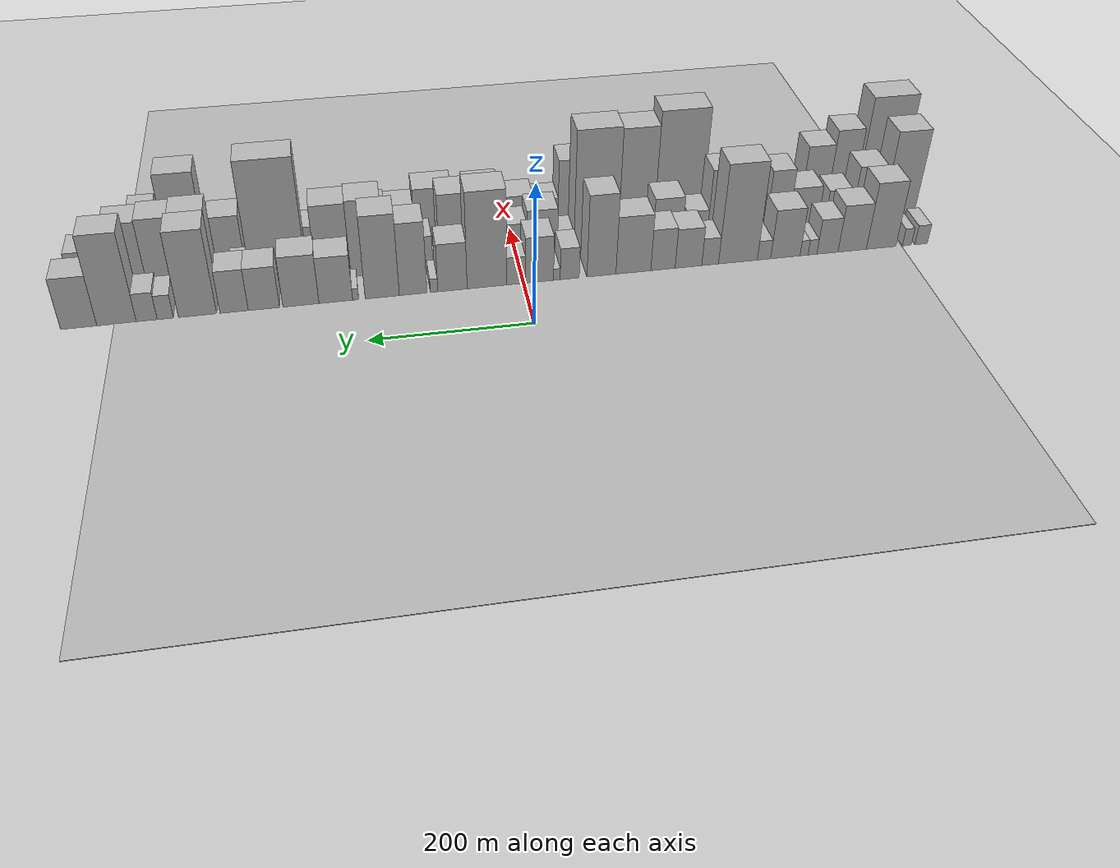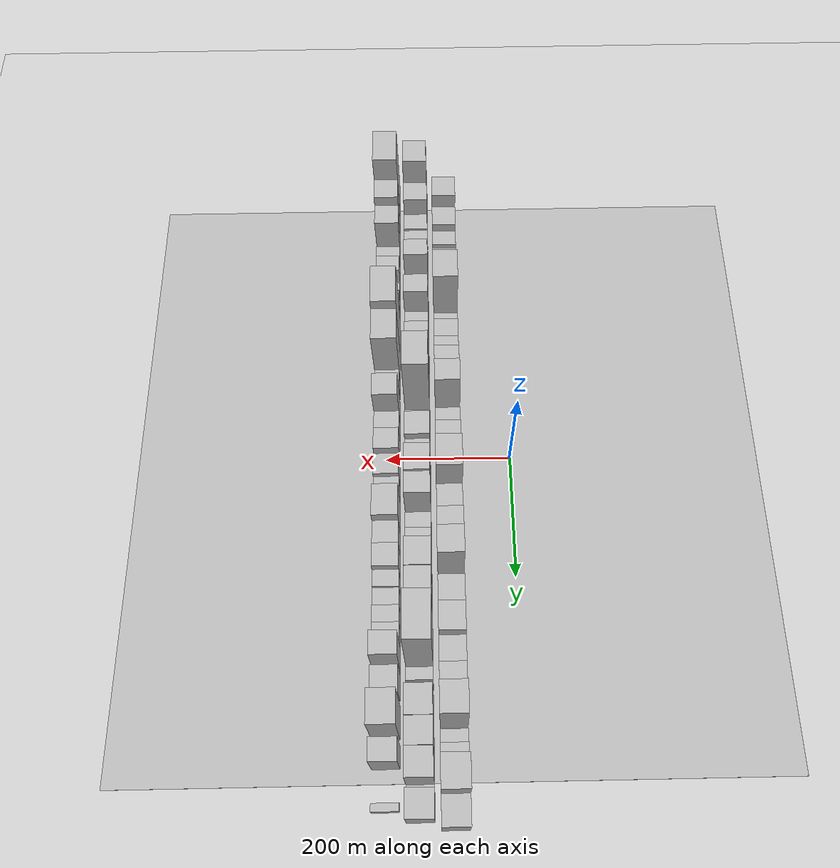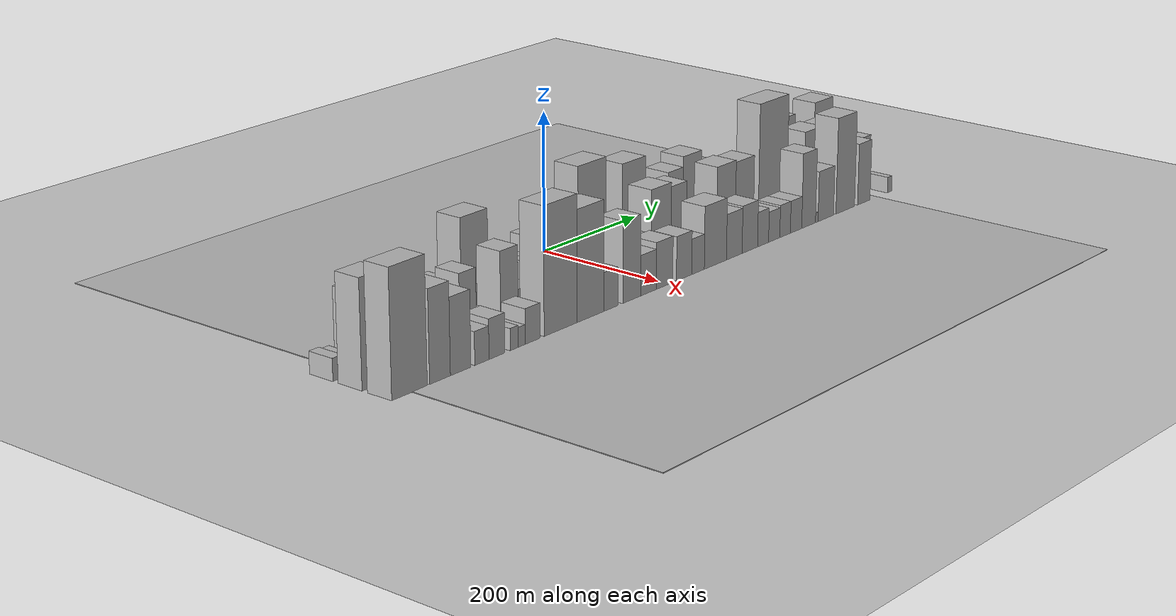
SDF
<?xml version="1.0" encoding="utf-8"?>

<sdf version="1.6">

   <world name="default">

      <gui fullscreen="0">

         <camera name="user_camera">

            <pose>-15 0 4.57585 0 0 0</pose>

            <view_controller>orbit</view_controller>

         </camera>

      </gui>

      <scene>

         <sky>

           <clouds>

             <speed>12</speed>

           </clouds>

         </sky>

         <ambient>0.4 0.4 0.4 1</ambient>

         <background>0.7 0.7 0.7 1</background>

         <shadows>1</shadows>

      </scene>

      <gravity>0 0 -9.8066</gravity>

      <magnetic_field>6e-06 2.3e-05 -4.2e-05</magnetic_field>

      <physics default="0" name="default_physics" type="ode">

         <ode>

            <solver>

               <type>quick</type>

               <iters>10</iters>

               <sor>1.0</sor>

               <use_dynamic_moi_rescaling>0</use_dynamic_moi_rescaling>

            </solver>

            <constraints>

               <cfm>0</cfm>

               <erp>0.2</erp>

               <contact_max_correcting_vel>100</contact_max_correcting_vel>

               <contact_surface_layer>0.001</contact_surface_layer>

            </constraints>

         </ode>

         <max_step_size>0.004</max_step_size>

         <real_time_factor>1</real_time_factor>

         <real_time_update_rate>250</real_time_update_rate>

      </physics>

      <light name="sun" type="directional">

         <cast_shadows>1</cast_shadows>

         <pose>0 0 10 0 0 0</pose>

         <diffuse>0.8 0.8 0.8 1</diffuse>

         <specular>0.2 0.2 0.2 1</specular>

         <attenuation>

            <range>1000</range>

            <constant>0.9</constant>

            <linear>0.01</linear>

            <quadratic>0.001</quadratic>

         </attenuation>

         <direction>-0.5 0.1 -0.9</direction>

      </light>

      <include>

         <name>ground_plane_1</name>

         <uri>model://HANNAS_ground_plane</uri>

         <pose>0 0 0  0 0 0</pose>

      </include>

      <include>

         <name>ground_plane_2</name>

         <uri>model://HANNAS_ground_plane</uri>

         <pose>100 0 0  0 0 0</pose>

      </include>

      <model name="building_1">

         <static>1</static>

         <pose frame="">100.0000 -527.3287 0 0.000000 0.000000 0.000000</pose>

         <link name="link">

            <pose frame="">0 0 15.00 0 0 0</pose>

            <collision name="collision">

               <geometry>

                  <box>

                     <size>40.0000 17.3426 30.0000</size>

                  </box>

               </geometry>

               <max_contacts>10</max_contacts>

               <surface>

                  <contact>

                     <ode/>

                  </contact>

                  <bounce/>

                  <friction>

                     <torsional>

                        <ode/>

                     </torsional>

                     <ode/>

                  </friction>

               </surface>

            </collision>

            <visual name="visual">

               <cast_shadows>0</cast_shadows>

               <geometry>

                  <box>

                     <size>40.0000 17.3426 30.0000</size>

                  </box>

               </geometry>

               <material>

                  <script>

                     <uri>model://HANNAS_wall/materials/scripts</uri>

                     <uri>model://HANNAS_wall/materials/textures</uri>

                     <name>vrc/HANNAS_wall</name>

                  </script>

               </material>

            </visual>

            <self_collide>0</self_collide>

            <enable_wind>0</enable_wind>

            <kinematic>0</kinematic>

         </link>

      </model>

      <model name="building_2">

         <static>1</static>

         <pose frame="">100.0000 -507.4993 0 0.000000 0.000000 0.000000</pose>

         <link name="link">

            <pose frame="">0 0 13.50 0 0 0</pose>

            <collision name="collision">

               <geometry>

                  <box>

                     <size>40.0000 12.3162 27.0000</size>

                  </box>

               </geometry>

               <max_contacts>10</max_contacts>

               <surface>

                  <contact>

                     <ode/>

                  </contact>

                  <bounce/>

                  <friction>

                     <torsional>

                        <ode/>

                     </torsional>

                     <ode/>

                  </friction>

               </surface>

            </collision>

            <visual name="visual">

               <cast_shadows>0</cast_shadows>

               <geometry>

                  <box>

                     <size>40.0000 12.3162 27.0000</size>

                  </box>

               </geometry>

               <material>

                  <script>

                     <uri>model://HANNAS_wall/materials/scripts</uri>

                     <uri>model://HANNAS_wall/materials/textures</uri>

                     <name>vrc/HANNAS_wall</name>

                  </script>

               </material>

            </visual>

            <self_collide>0</self_collide>

            <enable_wind>0</enable_wind>

            <kinematic>0</kinematic>

         </link>

      </model>

      <model name="building_3">

         <static>1</static>

         <pose frame="">100.0000 -472.0007 0 0.000000 0.000000 0.000000</pose>

         <link name="link">

            <pose frame="">0 0 51.00 0 0 0</pose>

            <collision name="collision">

               <geometry>

                  <box>

                     <size>40.0000 40.6811 102.0000</size>

                  </box>

               </geometry>

               <max_contacts>10</max_contacts>

               <surface>

                  <contact>

                     <ode/>

                  </contact>

                  <bounce/>

                  <friction>

                     <torsional>

                        <ode/>

                     </torsional>

                     <ode/>

                  </friction>

               </surface>

            </collision>

            <visual name="visual">

               <cast_shadows>0</cast_shadows>

               <geometry>

                  <box>

                     <size>40.0000 40.6811 102.0000</size>

                  </box>

               </geometry>

               <material>

                  <script>

                     <uri>model://HANNAS_wall/materials/scripts</uri>

                     <uri>model://HANNAS_wall/materials/textures</uri>

                     <name>vrc/HANNAS_wall</name>

                  </script>

               </material>

            </visual>

            <self_collide>0</self_collide>

            <enable_wind>0</enable_wind>

            <kinematic>0</kinematic>

         </link>

      </model>

      <model name="building_4">

         <static>1</static>

         <pose frame="">100.0000 -432.3073 0 0.000000 0.000000 0.000000</pose>

         <link name="link">

            <pose frame="">0 0 36.00 0 0 0</pose>

            <collision name="collision">

               <geometry>

                  <box>

                     <size>40.0000 38.7056 72.0000</size>

                  </box>

               </geometry>

               <max_contacts>10</max_contacts>

               <surface>

                  <contact>

                     <ode/>

                  </contact>

                  <bounce/>

                  <friction>

                     <torsional>

                        <ode/>

                     </torsional>

                     <ode/>

                  </friction>

               </surface>

            </collision>

            <visual name="visual">

               <cast_shadows>0</cast_shadows>

               <geometry>

                  <box>

                     <size>40.0000 38.7056 72.0000</size>

                  </box>

               </geometry>

               <material>

                  <script>

                     <uri>model://HANNAS_wall/materials/scripts</uri>

                     <uri>model://HANNAS_wall/materials/textures</uri>

                     <name>vrc/HANNAS_wall</name>

                  </script>

               </material>

            </visual>

            <self_collide>0</self_collide>

            <enable_wind>0</enable_wind>

            <kinematic>0</kinematic>

         </link>

      </model>

      <model name="building_5">

         <static>1</static>

         <pose frame="">100.0000 -398.5866 0 0.000000 0.000000 0.000000</pose>

         <link name="link">

            <pose frame="">0 0 27.00 0 0 0</pose>

            <collision name="collision">

               <geometry>

                  <box>

                     <size>40.0000 28.7358 54.0000</size>

                  </box>

               </geometry>

               <max_contacts>10</max_contacts>

               <surface>

                  <contact>

                     <ode/>

                  </contact>

                  <bounce/>

                  <friction>

                     <torsional>

                        <ode/>

                     </torsional>

                     <ode/>

                  </friction>

               </surface>

            </collision>

            <visual name="visual">

               <cast_shadows>0</cast_shadows>

               <geometry>

                  <box>

                     <size>40.0000 28.7358 54.0000</size>

                  </box>

               </geometry>

               <material>

                  <script>

                     <uri>model://HANNAS_wall/materials/scripts</uri>

                     <uri>model://HANNAS_wall/materials/textures</uri>

                     <name>vrc/HANNAS_wall</name>

                  </script>

               </material>

            </visual>

            <self_collide>0</self_collide>

            <enable_wind>0</enable_wind>

            <kinematic>0</kinematic>

         </link>

      </model>

      <model name="building_6">

         <static>1</static>

         <pose frame="">100.0000 -378.2275 0 0.000000 0.000000 0.000000</pose>

         <link name="link">

            <pose frame="">0 0 12.00 0 0 0</pose>

            <collision name="collision">

               <geometry>

                  <box>

                     <size>40.0000 11.9825 24.0000</size>

                  </box>

               </geometry>

               <max_contacts>10</max_contacts>

               <surface>

                  <contact>

                     <ode/>

                  </contact>

                  <bounce/>

                  <friction>

                     <torsional>

                        <ode/>

                     </torsional>

                     <ode/>

                  </friction>

               </surface>

            </collision>

            <visual name="visual">

               <cast_shadows>0</cast_shadows>

               <geometry>

                  <box>

                     <size>40.0000 11.9825 24.0000</size>

                  </box>

               </geometry>

               <material>

                  <script>

                     <uri>model://HANNAS_wall/materials/scripts</uri>

                     <uri>model://HANNAS_wall/materials/textures</uri>

                     <name>vrc/HANNAS_wall</name>

                  </script>

               </material>

            </visual>

            <self_collide>0</self_collide>

            <enable_wind>0</enable_wind>

            <kinematic>0</kinematic>

         </link>

      </model>

      <model name="building_7">

         <static>1</static>

         <pose frame="">100.0000 -366.8585 0 0.000000 0.000000 0.000000</pose>

         <link name="link">

            <pose frame="">0 0 12.00 0 0 0</pose>

            <collision name="collision">

               <geometry>

                  <box>

                     <size>40.0000 10.7555 24.0000</size>

                  </box>

               </geometry>

               <max_contacts>10</max_contacts>

               <surface>

                  <contact>

                     <ode/>

                  </contact>

                  <bounce/>

                  <friction>

                     <torsional>

                        <ode/>

                     </torsional>

                     <ode/>

                  </friction>

               </surface>

            </collision>

            <visual name="visual">

               <cast_shadows>0</cast_shadows>

               <geometry>

                  <box>

                     <size>40.0000 10.7555 24.0000</size>

                  </box>

               </geometry>

               <material>

                  <script>

                     <uri>model://HANNAS_wall/materials/scripts</uri>

                     <uri>model://HANNAS_wall/materials/textures</uri>

                     <name>vrc/HANNAS_wall</name>

                  </script>

               </material>

            </visual>

            <self_collide>0</self_collide>

            <enable_wind>0</enable_wind>

            <kinematic>0</kinematic>

         </link>

      </model>

      <model name="building_8">

         <static>1</static>

         <pose frame="">100.0000 -341.6340 0 0.000000 0.000000 0.000000</pose>

         <link name="link">

            <pose frame="">0 0 37.50 0 0 0</pose>

            <collision name="collision">

               <geometry>

                  <box>

                     <size>40.0000 39.6934 75.0000</size>

                  </box>

               </geometry>

               <max_contacts>10</max_contacts>

               <surface>

                  <contact>

                     <ode/>

                  </contact>

                  <bounce/>

                  <friction>

                     <torsional>

                        <ode/>

                     </torsional>

                     <ode/>

                  </friction>

               </surface>

            </collision>

            <visual name="visual">

               <cast_shadows>0</cast_shadows>

               <geometry>

                  <box>

                     <size>40.0000 39.6934 75.0000</size>

                  </box>

               </geometry>

               <material>

                  <script>

                     <uri>model://HANNAS_wall/materials/scripts</uri>

                     <uri>model://HANNAS_wall/materials/textures</uri>

                     <name>vrc/HANNAS_wall</name>

                  </script>

               </material>

            </visual>

            <self_collide>0</self_collide>

            <enable_wind>0</enable_wind>

            <kinematic>0</kinematic>

         </link>

      </model>

      <model name="building_9">

         <static>1</static>

         <pose frame="">100.0000 -312.8995 0 0.000000 0.000000 0.000000</pose>

         <link name="link">

            <pose frame="">0 0 15.00 0 0 0</pose>

            <collision name="collision">

               <geometry>

                  <box>

                     <size>40.0000 17.7757 30.0000</size>

                  </box>

               </geometry>

               <max_contacts>10</max_contacts>

               <surface>

                  <contact>

                     <ode/>

                  </contact>

                  <bounce/>

                  <friction>

                     <torsional>

                        <ode/>

                     </torsional>

                     <ode/>

                  </friction>

               </surface>

            </collision>

            <visual name="visual">

               <cast_shadows>0</cast_shadows>

               <geometry>

                  <box>

                     <size>40.0000 17.7757 30.0000</size>

                  </box>

               </geometry>

               <material>

                  <script>

                     <uri>model://HANNAS_wall/materials/scripts</uri>

                     <uri>model://HANNAS_wall/materials/textures</uri>

                     <name>vrc/HANNAS_wall</name>

                  </script>

               </material>

            </visual>

            <self_collide>0</self_collide>

            <enable_wind>0</enable_wind>

            <kinematic>0</kinematic>

         </link>

      </model>

      <model name="building_10">

         <static>1</static>

         <pose frame="">100.0000 -278.1690 0 0.000000 0.000000 0.000000</pose>

         <link name="link">

            <pose frame="">0 0 75.00 0 0 0</pose>

            <collision name="collision">

               <geometry>

                  <box>

                     <size>40.0000 51.6853 150.0000</size>

                  </box>

               </geometry>

               <max_contacts>10</max_contacts>

               <surface>

                  <contact>

                     <ode/>

                  </contact>

                  <bounce/>

                  <friction>

                     <torsional>

                        <ode/>

                     </torsional>

                     <ode/>

                  </friction>

               </surface>

            </collision>

            <visual name="visual">

               <cast_shadows>0</cast_shadows>

               <geometry>

                  <box>

                     <size>40.0000 51.6853 150.0000</size>

                  </box>

               </geometry>

               <material>

                  <script>

                     <uri>model://HANNAS_wall/materials/scripts</uri>

                     <uri>model://HANNAS_wall/materials/textures</uri>

                     <name>vrc/HANNAS_wall</name>

                  </script>

               </material>

            </visual>

            <self_collide>0</self_collide>

            <enable_wind>0</enable_wind>

            <kinematic>0</kinematic>

         </link>

      </model>

      <model name="building_11">

         <static>1</static>

         <pose frame="">100.0000 -241.2043 0 0.000000 0.000000 0.000000</pose>

         <link name="link">

            <pose frame="">0 0 21.00 0 0 0</pose>

            <collision name="collision">

               <geometry>

                  <box>

                     <size>40.0000 22.2441 42.0000</size>

                  </box>

               </geometry>

               <max_contacts>10</max_contacts>

               <surface>

                  <contact>

                     <ode/>

                  </contact>

                  <bounce/>

                  <friction>

                     <torsional>

                        <ode/>

                     </torsional>

                     <ode/>

                  </friction>

               </surface>

            </collision>

            <visual name="visual">

               <cast_shadows>0</cast_shadows>

               <geometry>

                  <box>

                     <size>40.0000 22.2441 42.0000</size>

                  </box>

               </geometry>

               <material>

                  <script>

                     <uri>model://HANNAS_wall/materials/scripts</uri>

                     <uri>model://HANNAS_wall/materials/textures</uri>

                     <name>vrc/HANNAS_wall</name>

                  </script>

               </material>

            </visual>

            <self_collide>0</self_collide>

            <enable_wind>0</enable_wind>

            <kinematic>0</kinematic>

         </link>

      </model>

      <model name="building_12">

         <static>1</static>

         <pose frame="">100.0000 -212.5697 0 0.000000 0.000000 0.000000</pose>

         <link name="link">

            <pose frame="">0 0 30.00 0 0 0</pose>

            <collision name="collision">

               <geometry>

                  <box>

                     <size>40.0000 35.0252 60.0000</size>

                  </box>

               </geometry>

               <max_contacts>10</max_contacts>

               <surface>

                  <contact>

                     <ode/>

                  </contact>

                  <bounce/>

                  <friction>

                     <torsional>

                        <ode/>

                     </torsional>

                     <ode/>

                  </friction>

               </surface>

            </collision>

            <visual name="visual">

               <cast_shadows>0</cast_shadows>

               <geometry>

                  <box>

                     <size>40.0000 35.0252 60.0000</size>

                  </box>

               </geometry>

               <material>

                  <script>

                     <uri>model://HANNAS_wall/materials/scripts</uri>

                     <uri>model://HANNAS_wall/materials/textures</uri>

                     <name>vrc/HANNAS_wall</name>

                  </script>

               </material>

            </visual>

            <self_collide>0</self_collide>

            <enable_wind>0</enable_wind>

            <kinematic>0</kinematic>

         </link>

      </model>

      <model name="building_13">

         <static>1</static>

         <pose frame="">100.0000 -179.1213 0 0.000000 0.000000 0.000000</pose>

         <link name="link">

            <pose frame="">0 0 31.50 0 0 0</pose>

            <collision name="collision">

               <geometry>

                  <box>

                     <size>40.0000 31.8716 63.0000</size>

                  </box>

               </geometry>

               <max_contacts>10</max_contacts>

               <surface>

                  <contact>

                     <ode/>

                  </contact>

                  <bounce/>

                  <friction>

                     <torsional>

                        <ode/>

                     </torsional>

                     <ode/>

                  </friction>

               </surface>

            </collision>

            <visual name="visual">

               <cast_shadows>0</cast_shadows>

               <geometry>

                  <box>

                     <size>40.0000 31.8716 63.0000</size>

                  </box>

               </geometry>

               <material>

                  <script>

                     <uri>model://HANNAS_wall/materials/scripts</uri>

                     <uri>model://HANNAS_wall/materials/textures</uri>

                     <name>vrc/HANNAS_wall</name>

                  </script>

               </material>

            </visual>

            <self_collide>0</self_collide>

            <enable_wind>0</enable_wind>

            <kinematic>0</kinematic>

         </link>

      </model>

      <model name="building_14">

         <static>1</static>

         <pose frame="">100.0000 -140.4751 0 0.000000 0.000000 0.000000</pose>

         <link name="link">

            <pose frame="">0 0 43.50 0 0 0</pose>

            <collision name="collision">

               <geometry>

                  <box>

                     <size>40.0000 45.4209 87.0000</size>

                  </box>

               </geometry>

               <max_contacts>10</max_contacts>

               <surface>

                  <contact>

                     <ode/>

                  </contact>

                  <bounce/>

                  <friction>

                     <torsional>

                        <ode/>

                     </torsional>

                     <ode/>

                  </friction>

               </surface>

            </collision>

            <visual name="visual">

               <cast_shadows>0</cast_shadows>

               <geometry>

                  <box>

                     <size>40.0000 45.4209 87.0000</size>

                  </box>

               </geometry>

               <material>

                  <script>

                     <uri>model://HANNAS_wall/materials/scripts</uri>

                     <uri>model://HANNAS_wall/materials/textures</uri>

                     <name>vrc/HANNAS_wall</name>

                  </script>

               </material>

            </visual>

            <self_collide>0</self_collide>

            <enable_wind>0</enable_wind>

            <kinematic>0</kinematic>

         </link>

      </model>

      <model name="building_15">

         <static>1</static>

         <pose frame="">100.0000 -99.0353 0 0.000000 0.000000 0.000000</pose>

         <link name="link">

            <pose frame="">0 0 61.50 0 0 0</pose>

            <collision name="collision">

               <geometry>

                  <box>

                     <size>40.0000 37.4587 123.0000</size>

                  </box>

               </geometry>

               <max_contacts>10</max_contacts>

               <surface>

                  <contact>

                     <ode/>

                  </contact>

                  <bounce/>

                  <friction>

                     <torsional>

                        <ode/>

                     </torsional>

                     <ode/>

                  </friction>

               </surface>

            </collision>

            <visual name="visual">

               <cast_shadows>0</cast_shadows>

               <geometry>

                  <box>

                     <size>40.0000 37.4587 123.0000</size>

                  </box>

               </geometry>

               <material>

                  <script>

                     <uri>model://HANNAS_wall/materials/scripts</uri>

                     <uri>model://HANNAS_wall/materials/textures</uri>

                     <name>vrc/HANNAS_wall</name>

                  </script>

               </material>

            </visual>

            <self_collide>0</self_collide>

            <enable_wind>0</enable_wind>

            <kinematic>0</kinematic>

         </link>

      </model>

      <model name="building_16">

         <static>1</static>

         <pose frame="">100.0000 -58.1016 0 0.000000 0.000000 0.000000</pose>

         <link name="link">

            <pose frame="">0 0 24.00 0 0 0</pose>

            <collision name="collision">

               <geometry>

                  <box>

                     <size>40.0000 24.4087 48.0000</size>

                  </box>

               </geometry>

               <max_contacts>10</max_contacts>

               <surface>

                  <contact>

                     <ode/>

                  </contact>

                  <bounce/>

                  <friction>

                     <torsional>

                        <ode/>

                     </torsional>

                     <ode/>

                  </friction>

               </surface>

            </collision>

            <visual name="visual">

               <cast_shadows>0</cast_shadows>

               <geometry>

                  <box>

                     <size>40.0000 24.4087 48.0000</size>

                  </box>

               </geometry>

               <material>

                  <script>

                     <uri>model://HANNAS_wall/materials/scripts</uri>

                     <uri>model://HANNAS_wall/materials/textures</uri>

                     <name>vrc/HANNAS_wall</name>

                  </script>

               </material>

            </visual>

            <self_collide>0</self_collide>

            <enable_wind>0</enable_wind>

            <kinematic>0</kinematic>

         </link>

      </model>

      <model name="building_17">

         <static>1</static>

         <pose frame="">100.0000 -41.6353 0 0.000000 0.000000 0.000000</pose>

         <link name="link">

            <pose frame="">0 0 9.00 0 0 0</pose>

            <collision name="collision">

               <geometry>

                  <box>

                     <size>40.0000 8.5240 18.0000</size>

                  </box>

               </geometry>

               <max_contacts>10</max_contacts>

               <surface>

                  <contact>

                     <ode/>

                  </contact>

                  <bounce/>

                  <friction>

                     <torsional>

                        <ode/>

                     </torsional>

                     <ode/>

                  </friction>

               </surface>

            </collision>

            <visual name="visual">

               <cast_shadows>0</cast_shadows>

               <geometry>

                  <box>

                     <size>40.0000 8.5240 18.0000</size>

                  </box>

               </geometry>

               <material>

                  <script>

                     <uri>model://HANNAS_wall/materials/scripts</uri>

                     <uri>model://HANNAS_wall/materials/textures</uri>

                     <name>vrc/HANNAS_wall</name>

                  </script>

               </material>

            </visual>

            <self_collide>0</self_collide>

            <enable_wind>0</enable_wind>

            <kinematic>0</kinematic>

         </link>

      </model>

      <model name="building_18">

         <static>1</static>

         <pose frame="">100.0000 -19.5050 0 0.000000 0.000000 0.000000</pose>

         <link name="link">

            <pose frame="">0 0 34.50 0 0 0</pose>

            <collision name="collision">

               <geometry>

                  <box>

                     <size>40.0000 35.7368 69.0000</size>

                  </box>

               </geometry>

               <max_contacts>10</max_contacts>

               <surface>

                  <contact>

                     <ode/>

                  </contact>

                  <bounce/>

                  <friction>

                     <torsional>

                        <ode/>

                     </torsional>

                     <ode/>

                  </friction>

               </surface>

            </collision>

            <visual name="visual">

               <cast_shadows>0</cast_shadows>

               <geometry>

                  <box>

                     <size>40.0000 35.7368 69.0000</size>

                  </box>

               </geometry>

               <material>

                  <script>

                     <uri>model://HANNAS_wall/materials/scripts</uri>

                     <uri>model://HANNAS_wall/materials/textures</uri>

                     <name>vrc/HANNAS_wall</name>

                  </script>

               </material>

            </visual>

            <self_collide>0</self_collide>

            <enable_wind>0</enable_wind>

            <kinematic>0</kinematic>

         </link>

      </model>

      <model name="building_19">

         <static>1</static>

         <pose frame="">100.0000 10.1503 0 0.000000 0.000000 0.000000</pose>

         <link name="link">

            <pose frame="">0 0 21.00 0 0 0</pose>

            <collision name="collision">

               <geometry>

                  <box>

                     <size>40.0000 23.5738 42.0000</size>

                  </box>

               </geometry>

               <max_contacts>10</max_contacts>

               <surface>

                  <contact>

                     <ode/>

                  </contact>

                  <bounce/>

                  <friction>

                     <torsional>

                        <ode/>

                     </torsional>

                     <ode/>

                  </friction>

               </surface>

            </collision>

            <visual name="visual">

               <cast_shadows>0</cast_shadows>

               <geometry>

                  <box>

                     <size>40.0000 23.5738 42.0000</size>

                  </box>

               </geometry>

               <material>

                  <script>

                     <uri>model://HANNAS_wall/materials/scripts</uri>

                     <uri>model://HANNAS_wall/materials/textures</uri>

                     <name>vrc/HANNAS_wall</name>

                  </script>

               </material>

            </visual>

            <self_collide>0</self_collide>

            <enable_wind>0</enable_wind>

            <kinematic>0</kinematic>

         </link>

      </model>

      <model name="building_20">

         <static>1</static>

         <pose frame="">100.0000 47.0468 0 0.000000 0.000000 0.000000</pose>

         <link name="link">

            <pose frame="">0 0 72.00 0 0 0</pose>

            <collision name="collision">

               <geometry>

                  <box>

                     <size>40.0000 50.2192 144.0000</size>

                  </box>

               </geometry>

               <max_contacts>10</max_contacts>

               <surface>

                  <contact>

                     <ode/>

                  </contact>

                  <bounce/>

                  <friction>

                     <torsional>

                        <ode/>

                     </torsional>

                     <ode/>

                  </friction>

               </surface>

            </collision>

            <visual name="visual">

               <cast_shadows>0</cast_shadows>

               <geometry>

                  <box>

                     <size>40.0000 50.2192 144.0000</size>

                  </box>

               </geometry>

               <material>

                  <script>

                     <uri>model://HANNAS_wall/materials/scripts</uri>

                     <uri>model://HANNAS_wall/materials/textures</uri>

                     <name>vrc/HANNAS_wall</name>

                  </script>

               </material>

            </visual>

            <self_collide>0</self_collide>

            <enable_wind>0</enable_wind>

            <kinematic>0</kinematic>

         </link>

      </model>

      <model name="building_21">

         <static>1</static>

         <pose frame="">100.0000 90.5522 0 0.000000 0.000000 0.000000</pose>

         <link name="link">

            <pose frame="">0 0 36.00 0 0 0</pose>

            <collision name="collision">

               <geometry>

                  <box>

                     <size>40.0000 36.7916 72.0000</size>

                  </box>

               </geometry>

               <max_contacts>10</max_contacts>

               <surface>

                  <contact>

                     <ode/>

                  </contact>

                  <bounce/>

                  <friction>

                     <torsional>

                        <ode/>

                     </torsional>

                     <ode/>

                  </friction>

               </surface>

            </collision>

            <visual name="visual">

               <cast_shadows>0</cast_shadows>

               <geometry>

                  <box>

                     <size>40.0000 36.7916 72.0000</size>

                  </box>

               </geometry>

               <material>

                  <script>

                     <uri>model://HANNAS_wall/materials/scripts</uri>

                     <uri>model://HANNAS_wall/materials/textures</uri>

                     <name>vrc/HANNAS_wall</name>

                  </script>

               </material>

            </visual>

            <self_collide>0</self_collide>

            <enable_wind>0</enable_wind>

            <kinematic>0</kinematic>

         </link>

      </model>

      <model name="building_22">

         <static>1</static>

         <pose frame="">100.0000 113.6437 0 0.000000 0.000000 0.000000</pose>

         <link name="link">

            <pose frame="">0 0 10.50 0 0 0</pose>

            <collision name="collision">

               <geometry>

                  <box>

                     <size>40.0000 9.3914 21.0000</size>

                  </box>

               </geometry>

               <max_contacts>10</max_contacts>

               <surface>

                  <contact>

                     <ode/>

                  </contact>

                  <bounce/>

                  <friction>

                     <torsional>

                        <ode/>

                     </torsional>

                     <ode/>

                  </friction>

               </surface>

            </collision>

            <visual name="visual">

               <cast_shadows>0</cast_shadows>

               <geometry>

                  <box>

                     <size>40.0000 9.3914 21.0000</size>

                  </box>

               </geometry>

               <material>

                  <script>

                     <uri>model://HANNAS_wall/materials/scripts</uri>

                     <uri>model://HANNAS_wall/materials/textures</uri>

                     <name>vrc/HANNAS_wall</name>

                  </script>

               </material>

            </visual>

            <self_collide>0</self_collide>

            <enable_wind>0</enable_wind>

            <kinematic>0</kinematic>

         </link>

      </model>

      <model name="building_23">

         <static>1</static>

         <pose frame="">100.0000 139.5569 0 0.000000 0.000000 0.000000</pose>

         <link name="link">

            <pose frame="">0 0 54.00 0 0 0</pose>

            <collision name="collision">

               <geometry>

                  <box>

                     <size>40.0000 34.4349 108.0000</size>

                  </box>

               </geometry>

               <max_contacts>10</max_contacts>

               <surface>

                  <contact>

                     <ode/>

                  </contact>

                  <bounce/>

                  <friction>

                     <torsional>

                        <ode/>

                     </torsional>

                     <ode/>

                  </friction>

               </surface>

            </collision>

            <visual name="visual">

               <cast_shadows>0</cast_shadows>

               <geometry>

                  <box>

                     <size>40.0000 34.4349 108.0000</size>

                  </box>

               </geometry>

               <material>

                  <script>

                     <uri>model://HANNAS_wall/materials/scripts</uri>

                     <uri>model://HANNAS_wall/materials/textures</uri>

                     <name>vrc/HANNAS_wall</name>

                  </script>

               </material>

            </visual>

            <self_collide>0</self_collide>

            <enable_wind>0</enable_wind>

            <kinematic>0</kinematic>

         </link>

      </model>

      <model name="building_24">

         <static>1</static>

         <pose frame="">100.0000 177.8657 0 0.000000 0.000000 0.000000</pose>

         <link name="link">

            <pose frame="">0 0 61.50 0 0 0</pose>

            <collision name="collision">

               <geometry>

                  <box>

                     <size>40.0000 42.1828 123.0000</size>

                  </box>

               </geometry>

               <max_contacts>10</max_contacts>

               <surface>

                  <contact>

                     <ode/>

                  </contact>

                  <bounce/>

                  <friction>

                     <torsional>

                        <ode/>

                     </torsional>

                     <ode/>

                  </friction>

               </surface>

            </collision>

            <visual name="visual">

               <cast_shadows>0</cast_shadows>

               <geometry>

                  <box>

                     <size>40.0000 42.1828 123.0000</size>

                  </box>

               </geometry>

               <material>

                  <script>

                     <uri>model://HANNAS_wall/materials/scripts</uri>

                     <uri>model://HANNAS_wall/materials/textures</uri>

                     <name>vrc/HANNAS_wall</name>

                  </script>

               </material>

            </visual>

            <self_collide>0</self_collide>

            <enable_wind>0</enable_wind>

            <kinematic>0</kinematic>

         </link>

      </model>

      <model name="building_25">

         <static>1</static>

         <pose frame="">100.0000 210.6498 0 0.000000 0.000000 0.000000</pose>

         <link name="link">

            <pose frame="">0 0 9.00 0 0 0</pose>

            <collision name="collision">

               <geometry>

                  <box>

                     <size>40.0000 7.3854 18.0000</size>

                  </box>

               </geometry>

               <max_contacts>10</max_contacts>

               <surface>

                  <contact>

                     <ode/>

                  </contact>

                  <bounce/>

                  <friction>

                     <torsional>

                        <ode/>

                     </torsional>

                     <ode/>

                  </friction>

               </surface>

            </collision>

            <visual name="visual">

               <cast_shadows>0</cast_shadows>

               <geometry>

                  <box>

                     <size>40.0000 7.3854 18.0000</size>

                  </box>

               </geometry>

               <material>

                  <script>

                     <uri>model://HANNAS_wall/materials/scripts</uri>

                     <uri>model://HANNAS_wall/materials/textures</uri>

                     <name>vrc/HANNAS_wall</name>

                  </script>

               </material>

            </visual>

            <self_collide>0</self_collide>

            <enable_wind>0</enable_wind>

            <kinematic>0</kinematic>

         </link>

      </model>

      <model name="building_26">

         <static>1</static>

         <pose frame="">100.0000 234.8787 0 0.000000 0.000000 0.000000</pose>

         <link name="link">

            <pose frame="">0 0 34.50 0 0 0</pose>

            <collision name="collision">

               <geometry>

                  <box>

                     <size>40.0000 41.0723 69.0000</size>

                  </box>

               </geometry>

               <max_contacts>10</max_contacts>

               <surface>

                  <contact>

                     <ode/>

                  </contact>

                  <bounce/>

                  <friction>

                     <torsional>

                        <ode/>

                     </torsional>

                     <ode/>

                  </friction>

               </surface>

            </collision>

            <visual name="visual">

               <cast_shadows>0</cast_shadows>

               <geometry>

                  <box>

                     <size>40.0000 41.0723 69.0000</size>

                  </box>

               </geometry>

               <material>

                  <script>

                     <uri>model://HANNAS_wall/materials/scripts</uri>

                     <uri>model://HANNAS_wall/materials/textures</uri>

                     <name>vrc/HANNAS_wall</name>

                  </script>

               </material>

            </visual>

            <self_collide>0</self_collide>

            <enable_wind>0</enable_wind>

            <kinematic>0</kinematic>

         </link>

      </model>

      <model name="building_27">

         <static>1</static>

         <pose frame="">100.0000 277.3453 0 0.000000 0.000000 0.000000</pose>

         <link name="link">

            <pose frame="">0 0 37.50 0 0 0</pose>

            <collision name="collision">

               <geometry>

                  <box>

                     <size>40.0000 43.8608 75.0000</size>

                  </box>

               </geometry>

               <max_contacts>10</max_contacts>

               <surface>

                  <contact>

                     <ode/>

                  </contact>

                  <bounce/>

                  <friction>

                     <torsional>

                        <ode/>

                     </torsional>

                     <ode/>

                  </friction>

               </surface>

            </collision>

            <visual name="visual">

               <cast_shadows>0</cast_shadows>

               <geometry>

                  <box>

                     <size>40.0000 43.8608 75.0000</size>

                  </box>

               </geometry>

               <material>

                  <script>

                     <uri>model://HANNAS_wall/materials/scripts</uri>

                     <uri>model://HANNAS_wall/materials/textures</uri>

                     <name>vrc/HANNAS_wall</name>

                  </script>

               </material>

            </visual>

            <self_collide>0</self_collide>

            <enable_wind>0</enable_wind>

            <kinematic>0</kinematic>

         </link>

      </model>

      <model name="building_28">

         <static>1</static>

         <pose frame="">100.0000 322.1616 0 0.000000 0.000000 0.000000</pose>

         <link name="link">

            <pose frame="">0 0 31.50 0 0 0</pose>

            <collision name="collision">

               <geometry>

                  <box>

                     <size>40.0000 37.7720 63.0000</size>

                  </box>

               </geometry>

               <max_contacts>10</max_contacts>

               <surface>

                  <contact>

                     <ode/>

                  </contact>

                  <bounce/>

                  <friction>

                     <torsional>

                        <ode/>

                     </torsional>

                     <ode/>

                  </friction>

               </surface>

            </collision>

            <visual name="visual">

               <cast_shadows>0</cast_shadows>

               <geometry>

                  <box>

                     <size>40.0000 37.7720 63.0000</size>

                  </box>

               </geometry>

               <material>

                  <script>

                     <uri>model://HANNAS_wall/materials/scripts</uri>

                     <uri>model://HANNAS_wall/materials/textures</uri>

                     <name>vrc/HANNAS_wall</name>

                  </script>

               </material>

            </visual>

            <self_collide>0</self_collide>

            <enable_wind>0</enable_wind>

            <kinematic>0</kinematic>

         </link>

      </model>

      <model name="building_29">

         <static>1</static>

         <pose frame="">100.0000 357.9804 0 0.000000 0.000000 0.000000</pose>

         <link name="link">

            <pose frame="">0 0 31.50 0 0 0</pose>

            <collision name="collision">

               <geometry>

                  <box>

                     <size>40.0000 33.8656 63.0000</size>

                  </box>

               </geometry>

               <max_contacts>10</max_contacts>

               <surface>

                  <contact>

                     <ode/>

                  </contact>

                  <bounce/>

                  <friction>

                     <torsional>

                        <ode/>

                     </torsional>

                     <ode/>

                  </friction>

               </surface>

            </collision>

            <visual name="visual">

               <cast_shadows>0</cast_shadows>

               <geometry>

                  <box>

                     <size>40.0000 33.8656 63.0000</size>

                  </box>

               </geometry>

               <material>

                  <script>

                     <uri>model://HANNAS_wall/materials/scripts</uri>

                     <uri>model://HANNAS_wall/materials/textures</uri>

                     <name>vrc/HANNAS_wall</name>

                  </script>

               </material>

            </visual>

            <self_collide>0</self_collide>

            <enable_wind>0</enable_wind>

            <kinematic>0</kinematic>

         </link>

      </model>

      <model name="building_30">

         <static>1</static>

         <pose frame="">100.0000 401.6068 0 0.000000 0.000000 0.000000</pose>

         <link name="link">

            <pose frame="">0 0 63.00 0 0 0</pose>

            <collision name="collision">

               <geometry>

                  <box>

                     <size>40.0000 45.3870 126.0000</size>

                  </box>

               </geometry>

               <max_contacts>10</max_contacts>

               <surface>

                  <contact>

                     <ode/>

                  </contact>

                  <bounce/>

                  <friction>

                     <torsional>

                        <ode/>

                     </torsional>

                     <ode/>

                  </friction>

               </surface>

            </collision>

            <visual name="visual">

               <cast_shadows>0</cast_shadows>

               <geometry>

                  <box>

                     <size>40.0000 45.3870 126.0000</size>

                  </box>

               </geometry>

               <material>

                  <script>

                     <uri>model://HANNAS_wall/materials/scripts</uri>

                     <uri>model://HANNAS_wall/materials/textures</uri>

                     <name>vrc/HANNAS_wall</name>

                  </script>

               </material>

            </visual>

            <self_collide>0</self_collide>

            <enable_wind>0</enable_wind>

            <kinematic>0</kinematic>

         </link>

      </model>

      <model name="building_31">

         <static>1</static>

         <pose frame="">100.0000 439.9004 0 0.000000 0.000000 0.000000</pose>

         <link name="link">

            <pose frame="">0 0 18.00 0 0 0</pose>

            <collision name="collision">

               <geometry>

                  <box>

                     <size>40.0000 19.2003 36.0000</size>

                  </box>

               </geometry>

               <max_contacts>10</max_contacts>

               <surface>

                  <contact>

                     <ode/>

                  </contact>

                  <bounce/>

                  <friction>

                     <torsional>

                        <ode/>

                     </torsional>

                     <ode/>

                  </friction>

               </surface>

            </collision>

            <visual name="visual">

               <cast_shadows>0</cast_shadows>

               <geometry>

                  <box>

                     <size>40.0000 19.2003 36.0000</size>

                  </box>

               </geometry>

               <material>

                  <script>

                     <uri>model://HANNAS_wall/materials/scripts</uri>

                     <uri>model://HANNAS_wall/materials/textures</uri>

                     <name>vrc/HANNAS_wall</name>

                  </script>

               </material>

            </visual>

            <self_collide>0</self_collide>

            <enable_wind>0</enable_wind>

            <kinematic>0</kinematic>

         </link>

      </model>

      <model name="building_32">

         <static>1</static>

         <pose frame="">100.0000 461.7719 0 0.000000 0.000000 0.000000</pose>

         <link name="link">

            <pose frame="">0 0 21.00 0 0 0</pose>

            <collision name="collision">

               <geometry>

                  <box>

                     <size>40.0000 24.5427 42.0000</size>

                  </box>

               </geometry>

               <max_contacts>10</max_contacts>

               <surface>

                  <contact>

                     <ode/>

                  </contact>

                  <bounce/>

                  <friction>

                     <torsional>

                        <ode/>

                     </torsional>

                     <ode/>

                  </friction>

               </surface>

            </collision>

            <visual name="visual">

               <cast_shadows>0</cast_shadows>

               <geometry>

                  <box>

                     <size>40.0000 24.5427 42.0000</size>

                  </box>

               </geometry>

               <material>

                  <script>

                     <uri>model://HANNAS_wall/materials/scripts</uri>

                     <uri>model://HANNAS_wall/materials/textures</uri>

                     <name>vrc/HANNAS_wall</name>

                  </script>

               </material>

            </visual>

            <self_collide>0</self_collide>

            <enable_wind>0</enable_wind>

            <kinematic>0</kinematic>

         </link>

      </model>

      <model name="building_33">

         <static>1</static>

         <pose frame="">100.0000 497.1217 0 0.000000 0.000000 0.000000</pose>

         <link name="link">

            <pose frame="">0 0 66.00 0 0 0</pose>

            <collision name="collision">

               <geometry>

                  <box>

                     <size>40.0000 46.1569 132.0000</size>

                  </box>

               </geometry>

               <max_contacts>10</max_contacts>

               <surface>

                  <contact>

                     <ode/>

                  </contact>

                  <bounce/>

                  <friction>

                     <torsional>

                        <ode/>

                     </torsional>

                     <ode/>

                  </friction>

               </surface>

            </collision>

            <visual name="visual">

               <cast_shadows>0</cast_shadows>

               <geometry>

                  <box>

                     <size>40.0000 46.1569 132.0000</size>

                  </box>

               </geometry>

               <material>

                  <script>

                     <uri>model://HANNAS_wall/materials/scripts</uri>

                     <uri>model://HANNAS_wall/materials/textures</uri>

                     <name>vrc/HANNAS_wall</name>

                  </script>

               </material>

            </visual>

            <self_collide>0</self_collide>

            <enable_wind>0</enable_wind>

            <kinematic>0</kinematic>

         </link>

      </model>

      <model name="building_34">

         <static>1</static>

         <pose frame="">100.0000 541.2689 0 0.000000 0.000000 0.000000</pose>

         <link name="link">

            <pose frame="">0 0 37.50 0 0 0</pose>

            <collision name="collision">

               <geometry>

                  <box>

                     <size>40.0000 42.1376 75.0000</size>

                  </box>

               </geometry>

               <max_contacts>10</max_contacts>

               <surface>

                  <contact>

                     <ode/>

                  </contact>

                  <bounce/>

                  <friction>

                     <torsional>

                        <ode/>

                     </torsional>

                     <ode/>

                  </friction>

               </surface>

            </collision>

            <visual name="visual">

               <cast_shadows>0</cast_shadows>

               <geometry>

                  <box>

                     <size>40.0000 42.1376 75.0000</size>

                  </box>

               </geometry>

               <material>

                  <script>

                     <uri>model://HANNAS_wall/materials/scripts</uri>

                     <uri>model://HANNAS_wall/materials/textures</uri>

                     <name>vrc/HANNAS_wall</name>

                  </script>

               </material>

            </visual>

            <self_collide>0</self_collide>

            <enable_wind>0</enable_wind>

            <kinematic>0</kinematic>

         </link>

      </model>

      <model name="building_35">

         <static>1</static>

         <pose frame="">149.0000 -513.6610 0 0.000000 0.000000 0.000000</pose>

         <link name="link">

            <pose frame="">0 0 72.00 0 0 0</pose>

            <collision name="collision">

               <geometry>

                  <box>

                     <size>40.0000 44.6781 144.0000</size>

                  </box>

               </geometry>

               <max_contacts>10</max_contacts>

               <surface>

                  <contact>

                     <ode/>

                  </contact>

                  <bounce/>

                  <friction>

                     <torsional>

                        <ode/>

                     </torsional>

                     <ode/>

                  </friction>

               </surface>

            </collision>

            <visual name="visual">

               <cast_shadows>0</cast_shadows>

               <geometry>

                  <box>

                     <size>40.0000 44.6781 144.0000</size>

                  </box>

               </geometry>

               <material>

                  <script>

                     <uri>model://HANNAS_wall/materials/scripts</uri>

                     <uri>model://HANNAS_wall/materials/textures</uri>

                     <name>vrc/HANNAS_wall</name>

                  </script>

               </material>

            </visual>

            <self_collide>0</self_collide>

            <enable_wind>0</enable_wind>

            <kinematic>0</kinematic>

         </link>

      </model>

      <model name="building_36">

         <static>1</static>

         <pose frame="">149.0000 -466.6545 0 0.000000 0.000000 0.000000</pose>

         <link name="link">

            <pose frame="">0 0 48.00 0 0 0</pose>

            <collision name="collision">

               <geometry>

                  <box>

                     <size>40.0000 37.3347 96.0000</size>

                  </box>

               </geometry>

               <max_contacts>10</max_contacts>

               <surface>

                  <contact>

                     <ode/>

                  </contact>

                  <bounce/>

                  <friction>

                     <torsional>

                        <ode/>

                     </torsional>

                     <ode/>

                  </friction>

               </surface>

            </collision>

            <visual name="visual">

               <cast_shadows>0</cast_shadows>

               <geometry>

                  <box>

                     <size>40.0000 37.3347 96.0000</size>

                  </box>

               </geometry>

               <material>

                  <script>

                     <uri>model://HANNAS_wall/materials/scripts</uri>

                     <uri>model://HANNAS_wall/materials/textures</uri>

                     <name>vrc/HANNAS_wall</name>

                  </script>

               </material>

            </visual>

            <self_collide>0</self_collide>

            <enable_wind>0</enable_wind>

            <kinematic>0</kinematic>

         </link>

      </model>

      <model name="building_37">

         <static>1</static>

         <pose frame="">149.0000 -427.1557 0 0.000000 0.000000 0.000000</pose>

         <link name="link">

            <pose frame="">0 0 31.50 0 0 0</pose>

            <collision name="collision">

               <geometry>

                  <box>

                     <size>40.0000 31.6630 63.0000</size>

                  </box>

               </geometry>

               <max_contacts>10</max_contacts>

               <surface>

                  <contact>

                     <ode/>

                  </contact>

                  <bounce/>

                  <friction>

                     <torsional>

                        <ode/>

                     </torsional>

                     <ode/>

                  </friction>

               </surface>

            </collision>

            <visual name="visual">

               <cast_shadows>0</cast_shadows>

               <geometry>

                  <box>

                     <size>40.0000 31.6630 63.0000</size>

                  </box>

               </geometry>

               <material>

                  <script>

                     <uri>model://HANNAS_wall/materials/scripts</uri>

                     <uri>model://HANNAS_wall/materials/textures</uri>

                     <name>vrc/HANNAS_wall</name>

                  </script>

               </material>

            </visual>

            <self_collide>0</self_collide>

            <enable_wind>0</enable_wind>

            <kinematic>0</kinematic>

         </link>

      </model>

      <model name="building_38">

         <static>1</static>

         <pose frame="">149.0000 -381.2080 0 0.000000 0.000000 0.000000</pose>

         <link name="link">

            <pose frame="">0 0 36.00 0 0 0</pose>

            <collision name="collision">

               <geometry>

                  <box>

                     <size>40.0000 40.2323 72.0000</size>

                  </box>

               </geometry>

               <max_contacts>10</max_contacts>

               <surface>

                  <contact>

                     <ode/>

                  </contact>

                  <bounce/>

                  <friction>

                     <torsional>

                        <ode/>

                     </torsional>

                     <ode/>

                  </friction>

               </surface>

            </collision>

            <visual name="visual">

               <cast_shadows>0</cast_shadows>

               <geometry>

                  <box>

                     <size>40.0000 40.2323 72.0000</size>

                  </box>

               </geometry>

               <material>

                  <script>

                     <uri>model://HANNAS_wall/materials/scripts</uri>

                     <uri>model://HANNAS_wall/materials/textures</uri>

                     <name>vrc/HANNAS_wall</name>

                  </script>

               </material>

            </visual>

            <self_collide>0</self_collide>

            <enable_wind>0</enable_wind>

            <kinematic>0</kinematic>

         </link>

      </model>

      <model name="building_39">

         <static>1</static>

         <pose frame="">149.0000 -345.5771 0 0.000000 0.000000 0.000000</pose>

         <link name="link">

            <pose frame="">0 0 51.00 0 0 0</pose>

            <collision name="collision">

               <geometry>

                  <box>

                     <size>40.0000 31.0294 102.0000</size>

                  </box>

               </geometry>

               <max_contacts>10</max_contacts>

               <surface>

                  <contact>

                     <ode/>

                  </contact>

                  <bounce/>

                  <friction>

                     <torsional>

                        <ode/>

                     </torsional>

                     <ode/>

                  </friction>

               </surface>

            </collision>

            <visual name="visual">

               <cast_shadows>0</cast_shadows>

               <geometry>

                  <box>

                     <size>40.0000 31.0294 102.0000</size>

                  </box>

               </geometry>

               <material>

                  <script>

                     <uri>model://HANNAS_wall/materials/scripts</uri>

                     <uri>model://HANNAS_wall/materials/textures</uri>

                     <name>vrc/HANNAS_wall</name>

                  </script>

               </material>

            </visual>

            <self_collide>0</self_collide>

            <enable_wind>0</enable_wind>

            <kinematic>0</kinematic>

         </link>

      </model>

      <model name="building_40">

         <static>1</static>

         <pose frame="">149.0000 -319.2591 0 0.000000 0.000000 0.000000</pose>

         <link name="link">

            <pose frame="">0 0 15.00 0 0 0</pose>

            <collision name="collision">

               <geometry>

                  <box>

                     <size>40.0000 15.6065 30.0000</size>

                  </box>

               </geometry>

               <max_contacts>10</max_contacts>

               <surface>

                  <contact>

                     <ode/>

                  </contact>

                  <bounce/>

                  <friction>

                     <torsional>

                        <ode/>

                     </torsional>

                     <ode/>

                  </friction>

               </surface>

            </collision>

            <visual name="visual">

               <cast_shadows>0</cast_shadows>

               <geometry>

                  <box>

                     <size>40.0000 15.6065 30.0000</size>

                  </box>

               </geometry>

               <material>

                  <script>

                     <uri>model://HANNAS_wall/materials/scripts</uri>

                     <uri>model://HANNAS_wall/materials/textures</uri>

                     <name>vrc/HANNAS_wall</name>

                  </script>

               </material>

            </visual>

            <self_collide>0</self_collide>

            <enable_wind>0</enable_wind>

            <kinematic>0</kinematic>

         </link>

      </model>

      <model name="building_41">

         <static>1</static>

         <pose frame="">149.0000 -306.5097 0 0.000000 0.000000 0.000000</pose>

         <link name="link">

            <pose frame="">0 0 12.00 0 0 0</pose>

            <collision name="collision">

               <geometry>

                  <box>

                     <size>40.0000 9.8923 24.0000</size>

                  </box>

               </geometry>

               <max_contacts>10</max_contacts>

               <surface>

                  <contact>

                     <ode/>

                  </contact>

                  <bounce/>

                  <friction>

                     <torsional>

                        <ode/>

                     </torsional>

                     <ode/>

                  </friction>

               </surface>

            </collision>

            <visual name="visual">

               <cast_shadows>0</cast_shadows>

               <geometry>

                  <box>

                     <size>40.0000 9.8923 24.0000</size>

                  </box>

               </geometry>

               <material>

                  <script>

                     <uri>model://HANNAS_wall/materials/scripts</uri>

                     <uri>model://HANNAS_wall/materials/textures</uri>

                     <name>vrc/HANNAS_wall</name>

                  </script>

               </material>

            </visual>

            <self_collide>0</self_collide>

            <enable_wind>0</enable_wind>

            <kinematic>0</kinematic>

         </link>

      </model>

      <model name="building_42">

         <static>1</static>

         <pose frame="">149.0000 -292.9622 0 0.000000 0.000000 0.000000</pose>

         <link name="link">

            <pose frame="">0 0 15.00 0 0 0</pose>

            <collision name="collision">

               <geometry>

                  <box>

                     <size>40.0000 17.2029 30.0000</size>

                  </box>

               </geometry>

               <max_contacts>10</max_contacts>

               <surface>

                  <contact>

                     <ode/>

                  </contact>

                  <bounce/>

                  <friction>

                     <torsional>

                        <ode/>

                     </torsional>

                     <ode/>

                  </friction>

               </surface>

            </collision>

            <visual name="visual">

               <cast_shadows>0</cast_shadows>

               <geometry>

                  <box>

                     <size>40.0000 17.2029 30.0000</size>

                  </box>

               </geometry>

               <material>

                  <script>

                     <uri>model://HANNAS_wall/materials/scripts</uri>

                     <uri>model://HANNAS_wall/materials/textures</uri>

                     <name>vrc/HANNAS_wall</name>

                  </script>

               </material>

            </visual>

            <self_collide>0</self_collide>

            <enable_wind>0</enable_wind>

            <kinematic>0</kinematic>

         </link>

      </model>

      <model name="building_43">

         <static>1</static>

         <pose frame="">149.0000 -267.3180 0 0.000000 0.000000 0.000000</pose>

         <link name="link">

            <pose frame="">0 0 55.50 0 0 0</pose>

            <collision name="collision">

               <geometry>

                  <box>

                     <size>40.0000 34.0854 111.0000</size>

                  </box>

               </geometry>

               <max_contacts>10</max_contacts>

               <surface>

                  <contact>

                     <ode/>

                  </contact>

                  <bounce/>

                  <friction>

                     <torsional>

                        <ode/>

                     </torsional>

                     <ode/>

                  </friction>

               </surface>

            </collision>

            <visual name="visual">

               <cast_shadows>0</cast_shadows>

               <geometry>

                  <box>

                     <size>40.0000 34.0854 111.0000</size>

                  </box>

               </geometry>

               <material>

                  <script>

                     <uri>model://HANNAS_wall/materials/scripts</uri>

                     <uri>model://HANNAS_wall/materials/textures</uri>

                     <name>vrc/HANNAS_wall</name>

                  </script>

               </material>

            </visual>

            <self_collide>0</self_collide>

            <enable_wind>0</enable_wind>

            <kinematic>0</kinematic>

         </link>

      </model>

      <model name="building_44">

         <static>1</static>

         <pose frame="">149.0000 -235.5309 0 0.000000 0.000000 0.000000</pose>

         <link name="link">

            <pose frame="">0 0 25.50 0 0 0</pose>

            <collision name="collision">

               <geometry>

                  <box>

                     <size>40.0000 29.4887 51.0000</size>

                  </box>

               </geometry>

               <max_contacts>10</max_contacts>

               <surface>

                  <contact>

                     <ode/>

                  </contact>

                  <bounce/>

                  <friction>

                     <torsional>

                        <ode/>

                     </torsional>

                     <ode/>

                  </friction>

               </surface>

            </collision>

            <visual name="visual">

               <cast_shadows>0</cast_shadows>

               <geometry>

                  <box>

                     <size>40.0000 29.4887 51.0000</size>

                  </box>

               </geometry>

               <material>

                  <script>

                     <uri>model://HANNAS_wall/materials/scripts</uri>

                     <uri>model://HANNAS_wall/materials/textures</uri>

                     <name>vrc/HANNAS_wall</name>

                  </script>

               </material>

            </visual>

            <self_collide>0</self_collide>

            <enable_wind>0</enable_wind>

            <kinematic>0</kinematic>

         </link>

      </model>

      <model name="building_45">

         <static>1</static>

         <pose frame="">149.0000 -197.1301 0 0.000000 0.000000 0.000000</pose>

         <link name="link">

            <pose frame="">0 0 37.50 0 0 0</pose>

            <collision name="collision">

               <geometry>

                  <box>

                     <size>40.0000 39.3130 75.0000</size>

                  </box>

               </geometry>

               <max_contacts>10</max_contacts>

               <surface>

                  <contact>

                     <ode/>

                  </contact>

                  <bounce/>

                  <friction>

                     <torsional>

                        <ode/>

                     </torsional>

                     <ode/>

                  </friction>

               </surface>

            </collision>

            <visual name="visual">

               <cast_shadows>0</cast_shadows>

               <geometry>

                  <box>

                     <size>40.0000 39.3130 75.0000</size>

                  </box>

               </geometry>

               <material>

                  <script>

                     <uri>model://HANNAS_wall/materials/scripts</uri>

                     <uri>model://HANNAS_wall/materials/textures</uri>

                     <name>vrc/HANNAS_wall</name>

                  </script>

               </material>

            </visual>

            <self_collide>0</self_collide>

            <enable_wind>0</enable_wind>

            <kinematic>0</kinematic>

         </link>

      </model>

      <model name="building_46">

         <static>1</static>

         <pose frame="">149.0000 -160.2968 0 0.000000 0.000000 0.000000</pose>

         <link name="link">

            <pose frame="">0 0 16.50 0 0 0</pose>

            <collision name="collision">

               <geometry>

                  <box>

                     <size>40.0000 18.3535 33.0000</size>

                  </box>

               </geometry>

               <max_contacts>10</max_contacts>

               <surface>

                  <contact>

                     <ode/>

                  </contact>

                  <bounce/>

                  <friction>

                     <torsional>

                        <ode/>

                     </torsional>

                     <ode/>

                  </friction>

               </surface>

            </collision>

            <visual name="visual">

               <cast_shadows>0</cast_shadows>

               <geometry>

                  <box>

                     <size>40.0000 18.3535 33.0000</size>

                  </box>

               </geometry>

               <material>

                  <script>

                     <uri>model://HANNAS_wall/materials/scripts</uri>

                     <uri>model://HANNAS_wall/materials/textures</uri>

                     <name>vrc/HANNAS_wall</name>

                  </script>

               </material>

            </visual>

            <self_collide>0</self_collide>

            <enable_wind>0</enable_wind>

            <kinematic>0</kinematic>

         </link>

      </model>

      <model name="building_47">

         <static>1</static>

         <pose frame="">149.0000 -140.8516 0 0.000000 0.000000 0.000000</pose>

         <link name="link">

            <pose frame="">0 0 18.00 0 0 0</pose>

            <collision name="collision">

               <geometry>

                  <box>

                     <size>40.0000 20.5370 36.0000</size>

                  </box>

               </geometry>

               <max_contacts>10</max_contacts>

               <surface>

                  <contact>

                     <ode/>

                  </contact>

                  <bounce/>

                  <friction>

                     <torsional>

                        <ode/>

                     </torsional>

                     <ode/>

                  </friction>

               </surface>

            </collision>

            <visual name="visual">

               <cast_shadows>0</cast_shadows>

               <geometry>

                  <box>

                     <size>40.0000 20.5370 36.0000</size>

                  </box>

               </geometry>

               <material>

                  <script>

                     <uri>model://HANNAS_wall/materials/scripts</uri>

                     <uri>model://HANNAS_wall/materials/textures</uri>

                     <name>vrc/HANNAS_wall</name>

                  </script>

               </material>

            </visual>

            <self_collide>0</self_collide>

            <enable_wind>0</enable_wind>

            <kinematic>0</kinematic>

         </link>

      </model>

      <model name="building_48">

         <static>1</static>

         <pose frame="">149.0000 -101.6946 0 0.000000 0.000000 0.000000</pose>

         <link name="link">

            <pose frame="">0 0 93.00 0 0 0</pose>

            <collision name="collision">

               <geometry>

                  <box>

                     <size>40.0000 57.7770 186.0000</size>

                  </box>

               </geometry>

               <max_contacts>10</max_contacts>

               <surface>

                  <contact>

                     <ode/>

                  </contact>

                  <bounce/>

                  <friction>

                     <torsional>

                        <ode/>

                     </torsional>

                     <ode/>

                  </friction>

               </surface>

            </collision>

            <visual name="visual">

               <cast_shadows>0</cast_shadows>

               <geometry>

                  <box>

                     <size>40.0000 57.7770 186.0000</size>

                  </box>

               </geometry>

               <material>

                  <script>

                     <uri>model://HANNAS_wall/materials/scripts</uri>

                     <uri>model://HANNAS_wall/materials/textures</uri>

                     <name>vrc/HANNAS_wall</name>

                  </script>

               </material>

            </visual>

            <self_collide>0</self_collide>

            <enable_wind>0</enable_wind>

            <kinematic>0</kinematic>

         </link>

      </model>

      <model name="building_49">

         <static>1</static>

         <pose frame="">149.0000 -62.0989 0 0.000000 0.000000 0.000000</pose>

         <link name="link">

            <pose frame="">0 0 18.00 0 0 0</pose>

            <collision name="collision">

               <geometry>

                  <box>

                     <size>40.0000 21.4145 36.0000</size>

                  </box>

               </geometry>

               <max_contacts>10</max_contacts>

               <surface>

                  <contact>

                     <ode/>

                  </contact>

                  <bounce/>

                  <friction>

                     <torsional>

                        <ode/>

                     </torsional>

                     <ode/>

                  </friction>

               </surface>

            </collision>

            <visual name="visual">

               <cast_shadows>0</cast_shadows>

               <geometry>

                  <box>

                     <size>40.0000 21.4145 36.0000</size>

                  </box>

               </geometry>

               <material>

                  <script>

                     <uri>model://HANNAS_wall/materials/scripts</uri>

                     <uri>model://HANNAS_wall/materials/textures</uri>

                     <name>vrc/HANNAS_wall</name>

                  </script>

               </material>

            </visual>

            <self_collide>0</self_collide>

            <enable_wind>0</enable_wind>

            <kinematic>0</kinematic>

         </link>

      </model>

      <model name="building_50">

         <static>1</static>

         <pose frame="">149.0000 -31.4144 0 0.000000 0.000000 0.000000</pose>

         <link name="link">

            <pose frame="">0 0 37.50 0 0 0</pose>

            <collision name="collision">

               <geometry>

                  <box>

                     <size>40.0000 39.9545 75.0000</size>

                  </box>

               </geometry>

               <max_contacts>10</max_contacts>

               <surface>

                  <contact>

                     <ode/>

                  </contact>

                  <bounce/>

                  <friction>

                     <torsional>

                        <ode/>

                     </torsional>

                     <ode/>

                  </friction>

               </surface>

            </collision>

            <visual name="visual">

               <cast_shadows>0</cast_shadows>

               <geometry>

                  <box>

                     <size>40.0000 39.9545 75.0000</size>

                  </box>

               </geometry>

               <material>

                  <script>

                     <uri>model://HANNAS_wall/materials/scripts</uri>

                     <uri>model://HANNAS_wall/materials/textures</uri>

                     <name>vrc/HANNAS_wall</name>

                  </script>

               </material>

            </visual>

            <self_collide>0</self_collide>

            <enable_wind>0</enable_wind>

            <kinematic>0</kinematic>

         </link>

      </model>

      <model name="building_51">

         <static>1</static>

         <pose frame="">149.0000 3.9588 0 0.000000 0.000000 0.000000</pose>

         <link name="link">

            <pose frame="">0 0 28.50 0 0 0</pose>

            <collision name="collision">

               <geometry>

                  <box>

                     <size>40.0000 30.7917 57.0000</size>

                  </box>

               </geometry>

               <max_contacts>10</max_contacts>

               <surface>

                  <contact>

                     <ode/>

                  </contact>

                  <bounce/>

                  <friction>

                     <torsional>

                        <ode/>

                     </torsional>

                     <ode/>

                  </friction>

               </surface>

            </collision>

            <visual name="visual">

               <cast_shadows>0</cast_shadows>

               <geometry>

                  <box>

                     <size>40.0000 30.7917 57.0000</size>

                  </box>

               </geometry>

               <material>

                  <script>

                     <uri>model://HANNAS_wall/materials/scripts</uri>

                     <uri>model://HANNAS_wall/materials/textures</uri>

                     <name>vrc/HANNAS_wall</name>

                  </script>

               </material>

            </visual>

            <self_collide>0</self_collide>

            <enable_wind>0</enable_wind>

            <kinematic>0</kinematic>

         </link>

      </model>

      <model name="building_52">

         <static>1</static>

         <pose frame="">149.0000 45.1882 0 0.000000 0.000000 0.000000</pose>

         <link name="link">

            <pose frame="">0 0 58.50 0 0 0</pose>

            <collision name="collision">

               <geometry>

                  <box>

                     <size>40.0000 43.6672 117.0000</size>

                  </box>

               </geometry>

               <max_contacts>10</max_contacts>

               <surface>

                  <contact>

                     <ode/>

                  </contact>

                  <bounce/>

                  <friction>

                     <torsional>

                        <ode/>

                     </torsional>

                     <ode/>

                  </friction>

               </surface>

            </collision>

            <visual name="visual">

               <cast_shadows>0</cast_shadows>

               <geometry>

                  <box>

                     <size>40.0000 43.6672 117.0000</size>

                  </box>

               </geometry>

               <material>

                  <script>

                     <uri>model://HANNAS_wall/materials/scripts</uri>

                     <uri>model://HANNAS_wall/materials/textures</uri>

                     <name>vrc/HANNAS_wall</name>

                  </script>

               </material>

            </visual>

            <self_collide>0</self_collide>

            <enable_wind>0</enable_wind>

            <kinematic>0</kinematic>

         </link>

      </model>

      <model name="building_53">

         <static>1</static>

         <pose frame="">149.0000 84.3158 0 0.000000 0.000000 0.000000</pose>

         <link name="link">

            <pose frame="">0 0 55.50 0 0 0</pose>

            <collision name="collision">

               <geometry>

                  <box>

                     <size>40.0000 34.5880 111.0000</size>

                  </box>

               </geometry>

               <max_contacts>10</max_contacts>

               <surface>

                  <contact>

                     <ode/>

                  </contact>

                  <bounce/>

                  <friction>

                     <torsional>

                        <ode/>

                     </torsional>

                     <ode/>

                  </friction>

               </surface>

            </collision>

            <visual name="visual">

               <cast_shadows>0</cast_shadows>

               <geometry>

                  <box>

                     <size>40.0000 34.5880 111.0000</size>

                  </box>

               </geometry>

               <material>

                  <script>

                     <uri>model://HANNAS_wall/materials/scripts</uri>

                     <uri>model://HANNAS_wall/materials/textures</uri>

                     <name>vrc/HANNAS_wall</name>

                  </script>

               </material>

            </visual>

            <self_collide>0</self_collide>

            <enable_wind>0</enable_wind>

            <kinematic>0</kinematic>

         </link>

      </model>

      <model name="building_54">

         <static>1</static>

         <pose frame="">149.0000 122.7011 0 0.000000 0.000000 0.000000</pose>

         <link name="link">

            <pose frame="">0 0 25.50 0 0 0</pose>

            <collision name="collision">

               <geometry>

                  <box>

                     <size>40.0000 26.1826 51.0000</size>

                  </box>

               </geometry>

               <max_contacts>10</max_contacts>

               <surface>

                  <contact>

                     <ode/>

                  </contact>

                  <bounce/>

                  <friction>

                     <torsional>

                        <ode/>

                     </torsional>

                     <ode/>

                  </friction>

               </surface>

            </collision>

            <visual name="visual">

               <cast_shadows>0</cast_shadows>

               <geometry>

                  <box>

                     <size>40.0000 26.1826 51.0000</size>

                  </box>

               </geometry>

               <material>

                  <script>

                     <uri>model://HANNAS_wall/materials/scripts</uri>

                     <uri>model://HANNAS_wall/materials/textures</uri>

                     <name>vrc/HANNAS_wall</name>

                  </script>

               </material>

            </visual>

            <self_collide>0</self_collide>

            <enable_wind>0</enable_wind>

            <kinematic>0</kinematic>

         </link>

      </model>

      <model name="building_55">

         <static>1</static>

         <pose frame="">149.0000 150.5972 0 0.000000 0.000000 0.000000</pose>

         <link name="link">

            <pose frame="">0 0 27.00 0 0 0</pose>

            <collision name="collision">

               <geometry>

                  <box>

                     <size>40.0000 29.6095 54.0000</size>

                  </box>

               </geometry>

               <max_contacts>10</max_contacts>

               <surface>

                  <contact>

                     <ode/>

                  </contact>

                  <bounce/>

                  <friction>

                     <torsional>

                        <ode/>

                     </torsional>

                     <ode/>

                  </friction>

               </surface>

            </collision>

            <visual name="visual">

               <cast_shadows>0</cast_shadows>

               <geometry>

                  <box>

                     <size>40.0000 29.6095 54.0000</size>

                  </box>

               </geometry>

               <material>

                  <script>

                     <uri>model://HANNAS_wall/materials/scripts</uri>

                     <uri>model://HANNAS_wall/materials/textures</uri>

                     <name>vrc/HANNAS_wall</name>

                  </script>

               </material>

            </visual>

            <self_collide>0</self_collide>

            <enable_wind>0</enable_wind>

            <kinematic>0</kinematic>

         </link>

      </model>

      <model name="building_56">

         <static>1</static>

         <pose frame="">149.0000 192.1033 0 0.000000 0.000000 0.000000</pose>

         <link name="link">

            <pose frame="">0 0 57.00 0 0 0</pose>

            <collision name="collision">

               <geometry>

                  <box>

                     <size>40.0000 43.4027 114.0000</size>

                  </box>

               </geometry>

               <max_contacts>10</max_contacts>

               <surface>

                  <contact>

                     <ode/>

                  </contact>

                  <bounce/>

                  <friction>

                     <torsional>

                        <ode/>

                     </torsional>

                     <ode/>

                  </friction>

               </surface>

            </collision>

            <visual name="visual">

               <cast_shadows>0</cast_shadows>

               <geometry>

                  <box>

                     <size>40.0000 43.4027 114.0000</size>

                  </box>

               </geometry>

               <material>

                  <script>

                     <uri>model://HANNAS_wall/materials/scripts</uri>

                     <uri>model://HANNAS_wall/materials/textures</uri>

                     <name>vrc/HANNAS_wall</name>

                  </script>

               </material>

            </visual>

            <self_collide>0</self_collide>

            <enable_wind>0</enable_wind>

            <kinematic>0</kinematic>

         </link>

      </model>

      <model name="building_57">

         <static>1</static>

         <pose frame="">149.0000 235.4099 0 0.000000 0.000000 0.000000</pose>

         <link name="link">

            <pose frame="">0 0 55.50 0 0 0</pose>

            <collision name="collision">

               <geometry>

                  <box>

                     <size>40.0000 43.2106 111.0000</size>

                  </box>

               </geometry>

               <max_contacts>10</max_contacts>

               <surface>

                  <contact>

                     <ode/>

                  </contact>

                  <bounce/>

                  <friction>

                     <torsional>

                        <ode/>

                     </torsional>

                     <ode/>

                  </friction>

               </surface>

            </collision>

            <visual name="visual">

               <cast_shadows>0</cast_shadows>

               <geometry>

                  <box>

                     <size>40.0000 43.2106 111.0000</size>

                  </box>

               </geometry>

               <material>

                  <script>

                     <uri>model://HANNAS_wall/materials/scripts</uri>

                     <uri>model://HANNAS_wall/materials/textures</uri>

                     <name>vrc/HANNAS_wall</name>

                  </script>

               </material>

            </visual>

            <self_collide>0</self_collide>

            <enable_wind>0</enable_wind>

            <kinematic>0</kinematic>

         </link>

      </model>

      <model name="building_58">

         <static>1</static>

         <pose frame="">149.0000 262.7709 0 0.000000 0.000000 0.000000</pose>

         <link name="link">

            <pose frame="">0 0 13.50 0 0 0</pose>

            <collision name="collision">

               <geometry>

                  <box>

                     <size>40.0000 11.5114 27.0000</size>

                  </box>

               </geometry>

               <max_contacts>10</max_contacts>

               <surface>

                  <contact>

                     <ode/>

                  </contact>

                  <bounce/>

                  <friction>

                     <torsional>

                        <ode/>

                     </torsional>

                     <ode/>

                  </friction>

               </surface>

            </collision>

            <visual name="visual">

               <cast_shadows>0</cast_shadows>

               <geometry>

                  <box>

                     <size>40.0000 11.5114 27.0000</size>

                  </box>

               </geometry>

               <material>

                  <script>

                     <uri>model://HANNAS_wall/materials/scripts</uri>

                     <uri>model://HANNAS_wall/materials/textures</uri>

                     <name>vrc/HANNAS_wall</name>

                  </script>

               </material>

            </visual>

            <self_collide>0</self_collide>

            <enable_wind>0</enable_wind>

            <kinematic>0</kinematic>

         </link>

      </model>

      <model name="building_59">

         <static>1</static>

         <pose frame="">149.0000 303.1798 0 0.000000 0.000000 0.000000</pose>

         <link name="link">

            <pose frame="">0 0 91.50 0 0 0</pose>

            <collision name="collision">

               <geometry>

                  <box>

                     <size>40.0000 69.3063 183.0000</size>

                  </box>

               </geometry>

               <max_contacts>10</max_contacts>

               <surface>

                  <contact>

                     <ode/>

                  </contact>

                  <bounce/>

                  <friction>

                     <torsional>

                        <ode/>

                     </torsional>

                     <ode/>

                  </friction>

               </surface>

            </collision>

            <visual name="visual">

               <cast_shadows>0</cast_shadows>

               <geometry>

                  <box>

                     <size>40.0000 69.3063 183.0000</size>

                  </box>

               </geometry>

               <material>

                  <script>

                     <uri>model://HANNAS_wall/materials/scripts</uri>

                     <uri>model://HANNAS_wall/materials/textures</uri>

                     <name>vrc/HANNAS_wall</name>

                  </script>

               </material>

            </visual>

            <self_collide>0</self_collide>

            <enable_wind>0</enable_wind>

            <kinematic>0</kinematic>

         </link>

      </model>

      <model name="building_60">

         <static>1</static>

         <pose frame="">149.0000 351.3624 0 0.000000 0.000000 0.000000</pose>

         <link name="link">

            <pose frame="">0 0 16.50 0 0 0</pose>

            <collision name="collision">

               <geometry>

                  <box>

                     <size>40.0000 19.0590 33.0000</size>

                  </box>

               </geometry>

               <max_contacts>10</max_contacts>

               <surface>

                  <contact>

                     <ode/>

                  </contact>

                  <bounce/>

                  <friction>

                     <torsional>

                        <ode/>

                     </torsional>

                     <ode/>

                  </friction>

               </surface>

            </collision>

            <visual name="visual">

               <cast_shadows>0</cast_shadows>

               <geometry>

                  <box>

                     <size>40.0000 19.0590 33.0000</size>

                  </box>

               </geometry>

               <material>

                  <script>

                     <uri>model://HANNAS_wall/materials/scripts</uri>

                     <uri>model://HANNAS_wall/materials/textures</uri>

                     <name>vrc/HANNAS_wall</name>

                  </script>

               </material>

            </visual>

            <self_collide>0</self_collide>

            <enable_wind>0</enable_wind>

            <kinematic>0</kinematic>

         </link>

      </model>

      <model name="building_61">

         <static>1</static>

         <pose frame="">149.0000 365.8853 0 0.000000 0.000000 0.000000</pose>

         <link name="link">

            <pose frame="">0 0 10.50 0 0 0</pose>

            <collision name="collision">

               <geometry>

                  <box>

                     <size>40.0000 9.9868 21.0000</size>

                  </box>

               </geometry>

               <max_contacts>10</max_contacts>

               <surface>

                  <contact>

                     <ode/>

                  </contact>

                  <bounce/>

                  <friction>

                     <torsional>

                        <ode/>

                     </torsional>

                     <ode/>

                  </friction>

               </surface>

            </collision>

            <visual name="visual">

               <cast_shadows>0</cast_shadows>

               <geometry>

                  <box>

                     <size>40.0000 9.9868 21.0000</size>

                  </box>

               </geometry>

               <material>

                  <script>

                     <uri>model://HANNAS_wall/materials/scripts</uri>

                     <uri>model://HANNAS_wall/materials/textures</uri>

                     <name>vrc/HANNAS_wall</name>

                  </script>

               </material>

            </visual>

            <self_collide>0</self_collide>

            <enable_wind>0</enable_wind>

            <kinematic>0</kinematic>

         </link>

      </model>

      <model name="building_62">

         <static>1</static>

         <pose frame="">149.0000 402.1342 0 0.000000 0.000000 0.000000</pose>

         <link name="link">

            <pose frame="">0 0 58.50 0 0 0</pose>

            <collision name="collision">

               <geometry>

                  <box>

                     <size>40.0000 42.5109 117.0000</size>

                  </box>

               </geometry>

               <max_contacts>10</max_contacts>

               <surface>

                  <contact>

                     <ode/>

                  </contact>

                  <bounce/>

                  <friction>

                     <torsional>

                        <ode/>

                     </torsional>

                     <ode/>

                  </friction>

               </surface>

            </collision>

            <visual name="visual">

               <cast_shadows>0</cast_shadows>

               <geometry>

                  <box>

                     <size>40.0000 42.5109 117.0000</size>

                  </box>

               </geometry>

               <material>

                  <script>

                     <uri>model://HANNAS_wall/materials/scripts</uri>

                     <uri>model://HANNAS_wall/materials/textures</uri>

                     <name>vrc/HANNAS_wall</name>

                  </script>

               </material>

            </visual>

            <self_collide>0</self_collide>

            <enable_wind>0</enable_wind>

            <kinematic>0</kinematic>

         </link>

      </model>

      <model name="building_63">

         <static>1</static>

         <pose frame="">149.0000 442.7425 0 0.000000 0.000000 0.000000</pose>

         <link name="link">

            <pose frame="">0 0 57.00 0 0 0</pose>

            <collision name="collision">

               <geometry>

                  <box>

                     <size>40.0000 38.7058 114.0000</size>

                  </box>

               </geometry>

               <max_contacts>10</max_contacts>

               <surface>

                  <contact>

                     <ode/>

                  </contact>

                  <bounce/>

                  <friction>

                     <torsional>

                        <ode/>

                     </torsional>

                     <ode/>

                  </friction>

               </surface>

            </collision>

            <visual name="visual">

               <cast_shadows>0</cast_shadows>

               <geometry>

                  <box>

                     <size>40.0000 38.7058 114.0000</size>

                  </box>

               </geometry>

               <material>

                  <script>

                     <uri>model://HANNAS_wall/materials/scripts</uri>

                     <uri>model://HANNAS_wall/materials/textures</uri>

                     <name>vrc/HANNAS_wall</name>

                  </script>

               </material>

            </visual>

            <self_collide>0</self_collide>

            <enable_wind>0</enable_wind>

            <kinematic>0</kinematic>

         </link>

      </model>

      <model name="building_64">

         <static>1</static>

         <pose frame="">149.0000 482.3765 0 0.000000 0.000000 0.000000</pose>

         <link name="link">

            <pose frame="">0 0 55.50 0 0 0</pose>

            <collision name="collision">

               <geometry>

                  <box>

                     <size>40.0000 40.5621 111.0000</size>

                  </box>

               </geometry>

               <max_contacts>10</max_contacts>

               <surface>

                  <contact>

                     <ode/>

                  </contact>

                  <bounce/>

                  <friction>

                     <torsional>

                        <ode/>

                     </torsional>

                     <ode/>

                  </friction>

               </surface>

            </collision>

            <visual name="visual">

               <cast_shadows>0</cast_shadows>

               <geometry>

                  <box>

                     <size>40.0000 40.5621 111.0000</size>

                  </box>

               </geometry>

               <material>

                  <script>

                     <uri>model://HANNAS_wall/materials/scripts</uri>

                     <uri>model://HANNAS_wall/materials/textures</uri>

                     <name>vrc/HANNAS_wall</name>

                  </script>

               </material>

            </visual>

            <self_collide>0</self_collide>

            <enable_wind>0</enable_wind>

            <kinematic>0</kinematic>

         </link>

      </model>

      <model name="building_65">

         <static>1</static>

         <pose frame="">149.0000 507.0143 0 0.000000 0.000000 0.000000</pose>

         <link name="link">

            <pose frame="">0 0 9.00 0 0 0</pose>

            <collision name="collision">

               <geometry>

                  <box>

                     <size>40.0000 8.7134 18.0000</size>

                  </box>

               </geometry>

               <max_contacts>10</max_contacts>

               <surface>

                  <contact>

                     <ode/>

                  </contact>

                  <bounce/>

                  <friction>

                     <torsional>

                        <ode/>

                     </torsional>

                     <ode/>

                  </friction>

               </surface>

            </collision>

            <visual name="visual">

               <cast_shadows>0</cast_shadows>

               <geometry>

                  <box>

                     <size>40.0000 8.7134 18.0000</size>

                  </box>

               </geometry>

               <material>

                  <script>

                     <uri>model://HANNAS_wall/materials/scripts</uri>

                     <uri>model://HANNAS_wall/materials/textures</uri>

                     <name>vrc/HANNAS_wall</name>

                  </script>

               </material>

            </visual>

            <self_collide>0</self_collide>

            <enable_wind>0</enable_wind>

            <kinematic>0</kinematic>

         </link>

      </model>

      <model name="building_66">

         <static>1</static>

         <pose frame="">149.0000 531.4093 0 0.000000 0.000000 0.000000</pose>

         <link name="link">

            <pose frame="">0 0 37.50 0 0 0</pose>

            <collision name="collision">

               <geometry>

                  <box>

                     <size>40.0000 40.0767 75.0000</size>

                  </box>

               </geometry>

               <max_contacts>10</max_contacts>

               <surface>

                  <contact>

                     <ode/>

                  </contact>

                  <bounce/>

                  <friction>

                     <torsional>

                        <ode/>

                     </torsional>

                     <ode/>

                  </friction>

               </surface>

            </collision>

            <visual name="visual">

               <cast_shadows>0</cast_shadows>

               <geometry>

                  <box>

                     <size>40.0000 40.0767 75.0000</size>

                  </box>

               </geometry>

               <material>

                  <script>

                     <uri>model://HANNAS_wall/materials/scripts</uri>

                     <uri>model://HANNAS_wall/materials/textures</uri>

                     <name>vrc/HANNAS_wall</name>

                  </script>

               </material>

            </visual>

            <self_collide>0</self_collide>

            <enable_wind>0</enable_wind>

            <kinematic>0</kinematic>

         </link>

      </model>

      <model name="building_67">

         <static>1</static>

         <pose frame="">198.0000 -504.9749 0 0.000000 0.000000 0.000000</pose>

         <link name="link">

            <pose frame="">0 0 84.00 0 0 0</pose>

            <collision name="collision">

               <geometry>

                  <box>

                     <size>40.0000 62.0502 168.0000</size>

                  </box>

               </geometry>

               <max_contacts>10</max_contacts>

               <surface>

                  <contact>

                     <ode/>

                  </contact>

                  <bounce/>

                  <friction>

                     <torsional>

                        <ode/>

                     </torsional>

                     <ode/>

                  </friction>

               </surface>

            </collision>

            <visual name="visual">

               <cast_shadows>0</cast_shadows>

               <geometry>

                  <box>

                     <size>40.0000 62.0502 168.0000</size>

                  </box>

               </geometry>

               <material>

                  <script>

                     <uri>model://HANNAS_wall/materials/scripts</uri>

                     <uri>model://HANNAS_wall/materials/textures</uri>

                     <name>vrc/HANNAS_wall</name>

                  </script>

               </material>

            </visual>

            <self_collide>0</self_collide>

            <enable_wind>0</enable_wind>

            <kinematic>0</kinematic>

         </link>

      </model>

      <model name="building_68">

         <static>1</static>

         <pose frame="">198.0000 -451.3016 0 0.000000 0.000000 0.000000</pose>

         <link name="link">

            <pose frame="">0 0 61.50 0 0 0</pose>

            <collision name="collision">

               <geometry>

                  <box>

                     <size>40.0000 37.2966 123.0000</size>

                  </box>

               </geometry>

               <max_contacts>10</max_contacts>

               <surface>

                  <contact>

                     <ode/>

                  </contact>

                  <bounce/>

                  <friction>

                     <torsional>

                        <ode/>

                     </torsional>

                     <ode/>

                  </friction>

               </surface>

            </collision>

            <visual name="visual">

               <cast_shadows>0</cast_shadows>

               <geometry>

                  <box>

                     <size>40.0000 37.2966 123.0000</size>

                  </box>

               </geometry>

               <material>

                  <script>

                     <uri>model://HANNAS_wall/materials/scripts</uri>

                     <uri>model://HANNAS_wall/materials/textures</uri>

                     <name>vrc/HANNAS_wall</name>

                  </script>

               </material>

            </visual>

            <self_collide>0</self_collide>

            <enable_wind>0</enable_wind>

            <kinematic>0</kinematic>

         </link>

      </model>

      <model name="building_69">

         <static>1</static>

         <pose frame="">198.0000 -414.0233 0 0.000000 0.000000 0.000000</pose>

         <link name="link">

            <pose frame="">0 0 51.00 0 0 0</pose>

            <collision name="collision">

               <geometry>

                  <box>

                     <size>40.0000 37.2601 102.0000</size>

                  </box>

               </geometry>

               <max_contacts>10</max_contacts>

               <surface>

                  <contact>

                     <ode/>

                  </contact>

                  <bounce/>

                  <friction>

                     <torsional>

                        <ode/>

                     </torsional>

                     <ode/>

                  </friction>

               </surface>

            </collision>

            <visual name="visual">

               <cast_shadows>0</cast_shadows>

               <geometry>

                  <box>

                     <size>40.0000 37.2601 102.0000</size>

                  </box>

               </geometry>

               <material>

                  <script>

                     <uri>model://HANNAS_wall/materials/scripts</uri>

                     <uri>model://HANNAS_wall/materials/textures</uri>

                     <name>vrc/HANNAS_wall</name>

                  </script>

               </material>

            </visual>

            <self_collide>0</self_collide>

            <enable_wind>0</enable_wind>

            <kinematic>0</kinematic>

         </link>

      </model>

      <model name="building_70">

         <static>1</static>

         <pose frame="">198.0000 -375.1692 0 0.000000 0.000000 0.000000</pose>

         <link name="link">

            <pose frame="">0 0 22.50 0 0 0</pose>

            <collision name="collision">

               <geometry>

                  <box>

                     <size>40.0000 26.4480 45.0000</size>

                  </box>

               </geometry>

               <max_contacts>10</max_contacts>

               <surface>

                  <contact>

                     <ode/>

                  </contact>

                  <bounce/>

                  <friction>

                     <torsional>

                        <ode/>

                     </torsional>

                     <ode/>

                  </friction>

               </surface>

            </collision>

            <visual name="visual">

               <cast_shadows>0</cast_shadows>

               <geometry>

                  <box>

                     <size>40.0000 26.4480 45.0000</size>

                  </box>

               </geometry>

               <material>

                  <script>

                     <uri>model://HANNAS_wall/materials/scripts</uri>

                     <uri>model://HANNAS_wall/materials/textures</uri>

                     <name>vrc/HANNAS_wall</name>

                  </script>

               </material>

            </visual>

            <self_collide>0</self_collide>

            <enable_wind>0</enable_wind>

            <kinematic>0</kinematic>

         </link>

      </model>

      <model name="building_71">

         <static>1</static>

         <pose frame="">198.0000 -347.0749 0 0.000000 0.000000 0.000000</pose>

         <link name="link">

            <pose frame="">0 0 27.00 0 0 0</pose>

            <collision name="collision">

               <geometry>

                  <box>

                     <size>40.0000 29.7407 54.0000</size>

                  </box>

               </geometry>

               <max_contacts>10</max_contacts>

               <surface>

                  <contact>

                     <ode/>

                  </contact>

                  <bounce/>

                  <friction>

                     <torsional>

                        <ode/>

                     </torsional>

                     <ode/>

                  </friction>

               </surface>

            </collision>

            <visual name="visual">

               <cast_shadows>0</cast_shadows>

               <geometry>

                  <box>

                     <size>40.0000 29.7407 54.0000</size>

                  </box>

               </geometry>

               <material>

                  <script>

                     <uri>model://HANNAS_wall/materials/scripts</uri>

                     <uri>model://HANNAS_wall/materials/textures</uri>

                     <name>vrc/HANNAS_wall</name>

                  </script>

               </material>

            </visual>

            <self_collide>0</self_collide>

            <enable_wind>0</enable_wind>

            <kinematic>0</kinematic>

         </link>

      </model>

      <model name="building_72">

         <static>1</static>

         <pose frame="">198.0000 -314.6844 0 0.000000 0.000000 0.000000</pose>

         <link name="link">

            <pose frame="">0 0 15.00 0 0 0</pose>

            <collision name="collision">

               <geometry>

                  <box>

                     <size>40.0000 15.0403 30.0000</size>

                  </box>

               </geometry>

               <max_contacts>10</max_contacts>

               <surface>

                  <contact>

                     <ode/>

                  </contact>

                  <bounce/>

                  <friction>

                     <torsional>

                        <ode/>

                     </torsional>

                     <ode/>

                  </friction>

               </surface>

            </collision>

            <visual name="visual">

               <cast_shadows>0</cast_shadows>

               <geometry>

                  <box>

                     <size>40.0000 15.0403 30.0000</size>

                  </box>

               </geometry>

               <material>

                  <script>

                     <uri>model://HANNAS_wall/materials/scripts</uri>

                     <uri>model://HANNAS_wall/materials/textures</uri>

                     <name>vrc/HANNAS_wall</name>

                  </script>

               </material>

            </visual>

            <self_collide>0</self_collide>

            <enable_wind>0</enable_wind>

            <kinematic>0</kinematic>

         </link>

      </model>

      <model name="building_73">

         <static>1</static>

         <pose frame="">198.0000 -300.4160 0 0.000000 0.000000 0.000000</pose>

         <link name="link">

            <pose frame="">0 0 13.50 0 0 0</pose>

            <collision name="collision">

               <geometry>

                  <box>

                     <size>40.0000 13.4965 27.0000</size>

                  </box>

               </geometry>

               <max_contacts>10</max_contacts>

               <surface>

                  <contact>

                     <ode/>

                  </contact>

                  <bounce/>

                  <friction>

                     <torsional>

                        <ode/>

                     </torsional>

                     <ode/>

                  </friction>

               </surface>

            </collision>

            <visual name="visual">

               <cast_shadows>0</cast_shadows>

               <geometry>

                  <box>

                     <size>40.0000 13.4965 27.0000</size>

                  </box>

               </geometry>

               <material>

                  <script>

                     <uri>model://HANNAS_wall/materials/scripts</uri>

                     <uri>model://HANNAS_wall/materials/textures</uri>

                     <name>vrc/HANNAS_wall</name>

                  </script>

               </material>

            </visual>

            <self_collide>0</self_collide>

            <enable_wind>0</enable_wind>

            <kinematic>0</kinematic>

         </link>

      </model>

      <model name="building_74">

         <static>1</static>

         <pose frame="">198.0000 -279.3317 0 0.000000 0.000000 0.000000</pose>

         <link name="link">

            <pose frame="">0 0 24.00 0 0 0</pose>

            <collision name="collision">

               <geometry>

                  <box>

                     <size>40.0000 28.6721 48.0000</size>

                  </box>

               </geometry>

               <max_contacts>10</max_contacts>

               <surface>

                  <contact>

                     <ode/>

                  </contact>

                  <bounce/>

                  <friction>

                     <torsional>

                        <ode/>

                     </torsional>

                     <ode/>

                  </friction>

               </surface>

            </collision>

            <visual name="visual">

               <cast_shadows>0</cast_shadows>

               <geometry>

                  <box>

                     <size>40.0000 28.6721 48.0000</size>

                  </box>

               </geometry>

               <material>

                  <script>

                     <uri>model://HANNAS_wall/materials/scripts</uri>

                     <uri>model://HANNAS_wall/materials/textures</uri>

                     <name>vrc/HANNAS_wall</name>

                  </script>

               </material>

            </visual>

            <self_collide>0</self_collide>

            <enable_wind>0</enable_wind>

            <kinematic>0</kinematic>

         </link>

      </model>

      <model name="building_75">

         <static>1</static>

         <pose frame="">198.0000 -224.3895 0 0.000000 0.000000 0.000000</pose>

         <link name="link">

            <pose frame="">0 0 87.00 0 0 0</pose>

            <collision name="collision">

               <geometry>

                  <box>

                     <size>40.0000 65.2123 174.0000</size>

                  </box>

               </geometry>

               <max_contacts>10</max_contacts>

               <surface>

                  <contact>

                     <ode/>

                  </contact>

                  <bounce/>

                  <friction>

                     <torsional>

                        <ode/>

                     </torsional>

                     <ode/>

                  </friction>

               </surface>

            </collision>

            <visual name="visual">

               <cast_shadows>0</cast_shadows>

               <geometry>

                  <box>

                     <size>40.0000 65.2123 174.0000</size>

                  </box>

               </geometry>

               <material>

                  <script>

                     <uri>model://HANNAS_wall/materials/scripts</uri>

                     <uri>model://HANNAS_wall/materials/textures</uri>

                     <name>vrc/HANNAS_wall</name>

                  </script>

               </material>

            </visual>

            <self_collide>0</self_collide>

            <enable_wind>0</enable_wind>

            <kinematic>0</kinematic>

         </link>

      </model>

      <model name="building_76">

         <static>1</static>

         <pose frame="">198.0000 -164.8681 0 0.000000 0.000000 0.000000</pose>

         <link name="link">

            <pose frame="">0 0 76.50 0 0 0</pose>

            <collision name="collision">

               <geometry>

                  <box>

                     <size>40.0000 53.8304 153.0000</size>

                  </box>

               </geometry>

               <max_contacts>10</max_contacts>

               <surface>

                  <contact>

                     <ode/>

                  </contact>

                  <bounce/>

                  <friction>

                     <torsional>

                        <ode/>

                     </torsional>

                     <ode/>

                  </friction>

               </surface>

            </collision>

            <visual name="visual">

               <cast_shadows>0</cast_shadows>

               <geometry>

                  <box>

                     <size>40.0000 53.8304 153.0000</size>

                  </box>

               </geometry>

               <material>

                  <script>

                     <uri>model://HANNAS_wall/materials/scripts</uri>

                     <uri>model://HANNAS_wall/materials/textures</uri>

                     <name>vrc/HANNAS_wall</name>

                  </script>

               </material>

            </visual>

            <self_collide>0</self_collide>

            <enable_wind>0</enable_wind>

            <kinematic>0</kinematic>

         </link>

      </model>

      <model name="building_77">

         <static>1</static>

         <pose frame="">198.0000 -123.2888 0 0.000000 0.000000 0.000000</pose>

         <link name="link">

            <pose frame="">0 0 27.00 0 0 0</pose>

            <collision name="collision">

               <geometry>

                  <box>

                     <size>40.0000 29.3283 54.0000</size>

                  </box>

               </geometry>

               <max_contacts>10</max_contacts>

               <surface>

                  <contact>

                     <ode/>

                  </contact>

                  <bounce/>

                  <friction>

                     <torsional>

                        <ode/>

                     </torsional>

                     <ode/>

                  </friction>

               </surface>

            </collision>

            <visual name="visual">

               <cast_shadows>0</cast_shadows>

               <geometry>

                  <box>

                     <size>40.0000 29.3283 54.0000</size>

                  </box>

               </geometry>

               <material>

                  <script>

                     <uri>model://HANNAS_wall/materials/scripts</uri>

                     <uri>model://HANNAS_wall/materials/textures</uri>

                     <name>vrc/HANNAS_wall</name>

                  </script>

               </material>

            </visual>

            <self_collide>0</self_collide>

            <enable_wind>0</enable_wind>

            <kinematic>0</kinematic>

         </link>

      </model>

      <model name="building_78">

         <static>1</static>

         <pose frame="">198.0000 -79.8004 0 0.000000 0.000000 0.000000</pose>

         <link name="link">

            <pose frame="">0 0 57.00 0 0 0</pose>

            <collision name="collision">

               <geometry>

                  <box>

                     <size>40.0000 37.6486 114.0000</size>

                  </box>

               </geometry>

               <max_contacts>10</max_contacts>

               <surface>

                  <contact>

                     <ode/>

                  </contact>

                  <bounce/>

                  <friction>

                     <torsional>

                        <ode/>

                     </torsional>

                     <ode/>

                  </friction>

               </surface>

            </collision>

            <visual name="visual">

               <cast_shadows>0</cast_shadows>

               <geometry>

                  <box>

                     <size>40.0000 37.6486 114.0000</size>

                  </box>

               </geometry>

               <material>

                  <script>

                     <uri>model://HANNAS_wall/materials/scripts</uri>

                     <uri>model://HANNAS_wall/materials/textures</uri>

                     <name>vrc/HANNAS_wall</name>

                  </script>

               </material>

            </visual>

            <self_collide>0</self_collide>

            <enable_wind>0</enable_wind>

            <kinematic>0</kinematic>

         </link>

      </model>

      <model name="building_79">

         <static>1</static>

         <pose frame="">198.0000 -44.2653 0 0.000000 0.000000 0.000000</pose>

         <link name="link">

            <pose frame="">0 0 28.50 0 0 0</pose>

            <collision name="collision">

               <geometry>

                  <box>

                     <size>40.0000 33.4216 57.0000</size>

                  </box>

               </geometry>

               <max_contacts>10</max_contacts>

               <surface>

                  <contact>

                     <ode/>

                  </contact>

                  <bounce/>

                  <friction>

                     <torsional>

                        <ode/>

                     </torsional>

                     <ode/>

                  </friction>

               </surface>

            </collision>

            <visual name="visual">

               <cast_shadows>0</cast_shadows>

               <geometry>

                  <box>

                     <size>40.0000 33.4216 57.0000</size>

                  </box>

               </geometry>

               <material>

                  <script>

                     <uri>model://HANNAS_wall/materials/scripts</uri>

                     <uri>model://HANNAS_wall/materials/textures</uri>

                     <name>vrc/HANNAS_wall</name>

                  </script>

               </material>

            </visual>

            <self_collide>0</self_collide>

            <enable_wind>0</enable_wind>

            <kinematic>0</kinematic>

         </link>

      </model>

      <model name="building_80">

         <static>1</static>

         <pose frame="">198.0000 -9.7621 0 0.000000 0.000000 0.000000</pose>

         <link name="link">

            <pose frame="">0 0 33.00 0 0 0</pose>

            <collision name="collision">

               <geometry>

                  <box>

                     <size>40.0000 35.5849 66.0000</size>

                  </box>

               </geometry>

               <max_contacts>10</max_contacts>

               <surface>

                  <contact>

                     <ode/>

                  </contact>

                  <bounce/>

                  <friction>

                     <torsional>

                        <ode/>

                     </torsional>

                     <ode/>

                  </friction>

               </surface>

            </collision>

            <visual name="visual">

               <cast_shadows>0</cast_shadows>

               <geometry>

                  <box>

                     <size>40.0000 35.5849 66.0000</size>

                  </box>

               </geometry>

               <material>

                  <script>

                     <uri>model://HANNAS_wall/materials/scripts</uri>

                     <uri>model://HANNAS_wall/materials/textures</uri>

                     <name>vrc/HANNAS_wall</name>

                  </script>

               </material>

            </visual>

            <self_collide>0</self_collide>

            <enable_wind>0</enable_wind>

            <kinematic>0</kinematic>

         </link>

      </model>

      <model name="building_81">

         <static>1</static>

         <pose frame="">198.0000 32.9275 0 0.000000 0.000000 0.000000</pose>

         <link name="link">

            <pose frame="">0 0 31.50 0 0 0</pose>

            <collision name="collision">

               <geometry>

                  <box>

                     <size>40.0000 33.7942 63.0000</size>

                  </box>

               </geometry>

               <max_contacts>10</max_contacts>

               <surface>

                  <contact>

                     <ode/>

                  </contact>

                  <bounce/>

                  <friction>

                     <torsional>

                        <ode/>

                     </torsional>

                     <ode/>

                  </friction>

               </surface>

            </collision>

            <visual name="visual">

               <cast_shadows>0</cast_shadows>

               <geometry>

                  <box>

                     <size>40.0000 33.7942 63.0000</size>

                  </box>

               </geometry>

               <material>

                  <script>

                     <uri>model://HANNAS_wall/materials/scripts</uri>

                     <uri>model://HANNAS_wall/materials/textures</uri>

                     <name>vrc/HANNAS_wall</name>

                  </script>

               </material>

            </visual>

            <self_collide>0</self_collide>

            <enable_wind>0</enable_wind>

            <kinematic>0</kinematic>

         </link>

      </model>

      <model name="building_82">

         <static>1</static>

         <pose frame="">198.0000 63.7659 0 0.000000 0.000000 0.000000</pose>

         <link name="link">

            <pose frame="">0 0 25.50 0 0 0</pose>

            <collision name="collision">

               <geometry>

                  <box>

                     <size>40.0000 27.8826 51.0000</size>

                  </box>

               </geometry>

               <max_contacts>10</max_contacts>

               <surface>

                  <contact>

                     <ode/>

                  </contact>

                  <bounce/>

                  <friction>

                     <torsional>

                        <ode/>

                     </torsional>

                     <ode/>

                  </friction>

               </surface>

            </collision>

            <visual name="visual">

               <cast_shadows>0</cast_shadows>

               <geometry>

                  <box>

                     <size>40.0000 27.8826 51.0000</size>

                  </box>

               </geometry>

               <material>

                  <script>

                     <uri>model://HANNAS_wall/materials/scripts</uri>

                     <uri>model://HANNAS_wall/materials/textures</uri>

                     <name>vrc/HANNAS_wall</name>

                  </script>

               </material>

            </visual>

            <self_collide>0</self_collide>

            <enable_wind>0</enable_wind>

            <kinematic>0</kinematic>

         </link>

      </model>

      <model name="building_83">

         <static>1</static>

         <pose frame="">198.0000 102.8362 0 0.000000 0.000000 0.000000</pose>

         <link name="link">

            <pose frame="">0 0 45.00 0 0 0</pose>

            <collision name="collision">

               <geometry>

                  <box>

                     <size>40.0000 50.2581 90.0000</size>

                  </box>

               </geometry>

               <max_contacts>10</max_contacts>

               <surface>

                  <contact>

                     <ode/>

                  </contact>

                  <bounce/>

                  <friction>

                     <torsional>

                        <ode/>

                     </torsional>

                     <ode/>

                  </friction>

               </surface>

            </collision>

            <visual name="visual">

               <cast_shadows>0</cast_shadows>

               <geometry>

                  <box>

                     <size>40.0000 50.2581 90.0000</size>

                  </box>

               </geometry>

               <material>

                  <script>

                     <uri>model://HANNAS_wall/materials/scripts</uri>

                     <uri>model://HANNAS_wall/materials/textures</uri>

                     <name>vrc/HANNAS_wall</name>

                  </script>

               </material>

            </visual>

            <self_collide>0</self_collide>

            <enable_wind>0</enable_wind>

            <kinematic>0</kinematic>

         </link>

      </model>

      <model name="building_84">

         <static>1</static>

         <pose frame="">198.0000 146.0418 0 0.000000 0.000000 0.000000</pose>

         <link name="link">

            <pose frame="">0 0 33.00 0 0 0</pose>

            <collision name="collision">

               <geometry>

                  <box>

                     <size>40.0000 36.1531 66.0000</size>

                  </box>

               </geometry>

               <max_contacts>10</max_contacts>

               <surface>

                  <contact>

                     <ode/>

                  </contact>

                  <bounce/>

                  <friction>

                     <torsional>

                        <ode/>

                     </torsional>

                     <ode/>

                  </friction>

               </surface>

            </collision>

            <visual name="visual">

               <cast_shadows>0</cast_shadows>

               <geometry>

                  <box>

                     <size>40.0000 36.1531 66.0000</size>

                  </box>

               </geometry>

               <material>

                  <script>

                     <uri>model://HANNAS_wall/materials/scripts</uri>

                     <uri>model://HANNAS_wall/materials/textures</uri>

                     <name>vrc/HANNAS_wall</name>

                  </script>

               </material>

            </visual>

            <self_collide>0</self_collide>

            <enable_wind>0</enable_wind>

            <kinematic>0</kinematic>

         </link>

      </model>

      <model name="building_85">

         <static>1</static>

         <pose frame="">198.0000 182.1685 0 0.000000 0.000000 0.000000</pose>

         <link name="link">

            <pose frame="">0 0 34.50 0 0 0</pose>

            <collision name="collision">

               <geometry>

                  <box>

                     <size>40.0000 36.1003 69.0000</size>

                  </box>

               </geometry>

               <max_contacts>10</max_contacts>

               <surface>

                  <contact>

                     <ode/>

                  </contact>

                  <bounce/>

                  <friction>

                     <torsional>

                        <ode/>

                     </torsional>

                     <ode/>

                  </friction>

               </surface>

            </collision>

            <visual name="visual">

               <cast_shadows>0</cast_shadows>

               <geometry>

                  <box>

                     <size>40.0000 36.1003 69.0000</size>

                  </box>

               </geometry>

               <material>

                  <script>

                     <uri>model://HANNAS_wall/materials/scripts</uri>

                     <uri>model://HANNAS_wall/materials/textures</uri>

                     <name>vrc/HANNAS_wall</name>

                  </script>

               </material>

            </visual>

            <self_collide>0</self_collide>

            <enable_wind>0</enable_wind>

            <kinematic>0</kinematic>

         </link>

      </model>

      <model name="building_86">

         <static>1</static>

         <pose frame="">198.0000 213.2985 0 0.000000 0.000000 0.000000</pose>

         <link name="link">

            <pose frame="">0 0 25.50 0 0 0</pose>

            <collision name="collision">

               <geometry>

                  <box>

                     <size>40.0000 26.1597 51.0000</size>

                  </box>

               </geometry>

               <max_contacts>10</max_contacts>

               <surface>

                  <contact>

                     <ode/>

                  </contact>

                  <bounce/>

                  <friction>

                     <torsional>

                        <ode/>

                     </torsional>

                     <ode/>

                  </friction>

               </surface>

            </collision>

            <visual name="visual">

               <cast_shadows>0</cast_shadows>

               <geometry>

                  <box>

                     <size>40.0000 26.1597 51.0000</size>

                  </box>

               </geometry>

               <material>

                  <script>

                     <uri>model://HANNAS_wall/materials/scripts</uri>

                     <uri>model://HANNAS_wall/materials/textures</uri>

                     <name>vrc/HANNAS_wall</name>

                  </script>

               </material>

            </visual>

            <self_collide>0</self_collide>

            <enable_wind>0</enable_wind>

            <kinematic>0</kinematic>

         </link>

      </model>

      <model name="building_87">

         <static>1</static>

         <pose frame="">198.0000 239.7685 0 0.000000 0.000000 0.000000</pose>

         <link name="link">

            <pose frame="">0 0 22.50 0 0 0</pose>

            <collision name="collision">

               <geometry>

                  <box>

                     <size>40.0000 26.7803 45.0000</size>

                  </box>

               </geometry>

               <max_contacts>10</max_contacts>

               <surface>

                  <contact>

                     <ode/>

                  </contact>

                  <bounce/>

                  <friction>

                     <torsional>

                        <ode/>

                     </torsional>

                     <ode/>

                  </friction>

               </surface>

            </collision>

            <visual name="visual">

               <cast_shadows>0</cast_shadows>

               <geometry>

                  <box>

                     <size>40.0000 26.7803 45.0000</size>

                  </box>

               </geometry>

               <material>

                  <script>

                     <uri>model://HANNAS_wall/materials/scripts</uri>

                     <uri>model://HANNAS_wall/materials/textures</uri>

                     <name>vrc/HANNAS_wall</name>

                  </script>

               </material>

            </visual>

            <self_collide>0</self_collide>

            <enable_wind>0</enable_wind>

            <kinematic>0</kinematic>

         </link>

      </model>

      <model name="building_88">

         <static>1</static>

         <pose frame="">198.0000 265.9663 0 0.000000 0.000000 0.000000</pose>

         <link name="link">

            <pose frame="">0 0 24.00 0 0 0</pose>

            <collision name="collision">

               <geometry>

                  <box>

                     <size>40.0000 25.6152 48.0000</size>

                  </box>

               </geometry>

               <max_contacts>10</max_contacts>

               <surface>

                  <contact>

                     <ode/>

                  </contact>

                  <bounce/>

                  <friction>

                     <torsional>

                        <ode/>

                     </torsional>

                     <ode/>

                  </friction>

               </surface>

            </collision>

            <visual name="visual">

               <cast_shadows>0</cast_shadows>

               <geometry>

                  <box>

                     <size>40.0000 25.6152 48.0000</size>

                  </box>

               </geometry>

               <material>

                  <script>

                     <uri>model://HANNAS_wall/materials/scripts</uri>

                     <uri>model://HANNAS_wall/materials/textures</uri>

                     <name>vrc/HANNAS_wall</name>

                  </script>

               </material>

            </visual>

            <self_collide>0</self_collide>

            <enable_wind>0</enable_wind>

            <kinematic>0</kinematic>

         </link>

      </model>

      <model name="building_89">

         <static>1</static>

         <pose frame="">198.0000 292.6292 0 0.000000 0.000000 0.000000</pose>

         <link name="link">

            <pose frame="">0 0 24.00 0 0 0</pose>

            <collision name="collision">

               <geometry>

                  <box>

                     <size>40.0000 27.7106 48.0000</size>

                  </box>

               </geometry>

               <max_contacts>10</max_contacts>

               <surface>

                  <contact>

                     <ode/>

                  </contact>

                  <bounce/>

                  <friction>

                     <torsional>

                        <ode/>

                     </torsional>

                     <ode/>

                  </friction>

               </surface>

            </collision>

            <visual name="visual">

               <cast_shadows>0</cast_shadows>

               <geometry>

                  <box>

                     <size>40.0000 27.7106 48.0000</size>

                  </box>

               </geometry>

               <material>

                  <script>

                     <uri>model://HANNAS_wall/materials/scripts</uri>

                     <uri>model://HANNAS_wall/materials/textures</uri>

                     <name>vrc/HANNAS_wall</name>

                  </script>

               </material>

            </visual>

            <self_collide>0</self_collide>

            <enable_wind>0</enable_wind>

            <kinematic>0</kinematic>

         </link>

      </model>

      <model name="building_90">

         <static>1</static>

         <pose frame="">198.0000 323.5039 0 0.000000 0.000000 0.000000</pose>

         <link name="link">

            <pose frame="">0 0 55.50 0 0 0</pose>

            <collision name="collision">

               <geometry>

                  <box>

                     <size>40.0000 34.0389 111.0000</size>

                  </box>

               </geometry>

               <max_contacts>10</max_contacts>

               <surface>

                  <contact>

                     <ode/>

                  </contact>

                  <bounce/>

                  <friction>

                     <torsional>

                        <ode/>

                     </torsional>

                     <ode/>

                  </friction>

               </surface>

            </collision>

            <visual name="visual">

               <cast_shadows>0</cast_shadows>

               <geometry>

                  <box>

                     <size>40.0000 34.0389 111.0000</size>

                  </box>

               </geometry>

               <material>

                  <script>

                     <uri>model://HANNAS_wall/materials/scripts</uri>

                     <uri>model://HANNAS_wall/materials/textures</uri>

                     <name>vrc/HANNAS_wall</name>

                  </script>

               </material>

            </visual>

            <self_collide>0</self_collide>

            <enable_wind>0</enable_wind>

            <kinematic>0</kinematic>

         </link>

      </model>

      <model name="building_91">

         <static>1</static>

         <pose frame="">198.0000 343.6524 0 0.000000 0.000000 0.000000</pose>

         <link name="link">

            <pose frame="">0 0 7.50 0 0 0</pose>

            <collision name="collision">

               <geometry>

                  <box>

                     <size>40.0000 6.2582 15.0000</size>

                  </box>

               </geometry>

               <max_contacts>10</max_contacts>

               <surface>

                  <contact>

                     <ode/>

                  </contact>

                  <bounce/>

                  <friction>

                     <torsional>

                        <ode/>

                     </torsional>

                     <ode/>

                  </friction>

               </surface>

            </collision>

            <visual name="visual">

               <cast_shadows>0</cast_shadows>

               <geometry>

                  <box>

                     <size>40.0000 6.2582 15.0000</size>

                  </box>

               </geometry>

               <material>

                  <script>

                     <uri>model://HANNAS_wall/materials/scripts</uri>

                     <uri>model://HANNAS_wall/materials/textures</uri>

                     <name>vrc/HANNAS_wall</name>

                  </script>

               </material>

            </visual>

            <self_collide>0</self_collide>

            <enable_wind>0</enable_wind>

            <kinematic>0</kinematic>

         </link>

      </model>

      <model name="building_92">

         <static>1</static>

         <pose frame="">198.0000 366.2807 0 0.000000 0.000000 0.000000</pose>

         <link name="link">

            <pose frame="">0 0 37.50 0 0 0</pose>

            <collision name="collision">

               <geometry>

                  <box>

                     <size>40.0000 38.9983 75.0000</size>

                  </box>

               </geometry>

               <max_contacts>10</max_contacts>

               <surface>

                  <contact>

                     <ode/>

                  </contact>

                  <bounce/>

                  <friction>

                     <torsional>

                        <ode/>

                     </torsional>

                     <ode/>

                  </friction>

               </surface>

            </collision>

            <visual name="visual">

               <cast_shadows>0</cast_shadows>

               <geometry>

                  <box>

                     <size>40.0000 38.9983 75.0000</size>

                  </box>

               </geometry>

               <material>

                  <script>

                     <uri>model://HANNAS_wall/materials/scripts</uri>

                     <uri>model://HANNAS_wall/materials/textures</uri>

                     <name>vrc/HANNAS_wall</name>

                  </script>

               </material>

            </visual>

            <self_collide>0</self_collide>

            <enable_wind>0</enable_wind>

            <kinematic>0</kinematic>

         </link>

      </model>

      <model name="building_93">

         <static>1</static>

         <pose frame="">198.0000 415.5931 0 0.000000 0.000000 0.000000</pose>

         <link name="link">

            <pose frame="">0 0 72.00 0 0 0</pose>

            <collision name="collision">

               <geometry>

                  <box>

                     <size>40.0000 47.6265 144.0000</size>

                  </box>

               </geometry>

               <max_contacts>10</max_contacts>

               <surface>

                  <contact>

                     <ode/>

                  </contact>

                  <bounce/>

                  <friction>

                     <torsional>

                        <ode/>

                     </torsional>

                     <ode/>

                  </friction>

               </surface>

            </collision>

            <visual name="visual">

               <cast_shadows>0</cast_shadows>

               <geometry>

                  <box>

                     <size>40.0000 47.6265 144.0000</size>

                  </box>

               </geometry>

               <material>

                  <script>

                     <uri>model://HANNAS_wall/materials/scripts</uri>

                     <uri>model://HANNAS_wall/materials/textures</uri>

                     <name>vrc/HANNAS_wall</name>

                  </script>

               </material>

            </visual>

            <self_collide>0</self_collide>

            <enable_wind>0</enable_wind>

            <kinematic>0</kinematic>

         </link>

      </model>

      <model name="building_94">

         <static>1</static>

         <pose frame="">198.0000 463.5687 0 0.000000 0.000000 0.000000</pose>

         <link name="link">

            <pose frame="">0 0 46.50 0 0 0</pose>

            <collision name="collision">

               <geometry>

                  <box>

                     <size>40.0000 32.3247 93.0000</size>

                  </box>

               </geometry>

               <max_contacts>10</max_contacts>

               <surface>

                  <contact>

                     <ode/>

                  </contact>

                  <bounce/>

                  <friction>

                     <torsional>

                        <ode/>

                     </torsional>

                     <ode/>

                  </friction>

               </surface>

            </collision>

            <visual name="visual">

               <cast_shadows>0</cast_shadows>

               <geometry>

                  <box>

                     <size>40.0000 32.3247 93.0000</size>

                  </box>

               </geometry>

               <material>

                  <script>

                     <uri>model://HANNAS_wall/materials/scripts</uri>

                     <uri>model://HANNAS_wall/materials/textures</uri>

                     <name>vrc/HANNAS_wall</name>

                  </script>

               </material>

            </visual>

            <self_collide>0</self_collide>

            <enable_wind>0</enable_wind>

            <kinematic>0</kinematic>

         </link>

      </model>

      <model name="building_95">

         <static>1</static>

         <pose frame="">198.0000 531.8672 0 0.000000 0.000000 0.000000</pose>

         <link name="link">

            <pose frame="">0 0 12.00 0 0 0</pose>

            <collision name="collision">

               <geometry>

                  <box>

                     <size>40.0000 11.4241 24.0000</size>

                  </box>

               </geometry>

               <max_contacts>10</max_contacts>

               <surface>

                  <contact>

                     <ode/>

                  </contact>

                  <bounce/>

                  <friction>

                     <torsional>

                        <ode/>

                     </torsional>

                     <ode/>

                  </friction>

               </surface>

            </collision>

            <visual name="visual">

               <cast_shadows>0</cast_shadows>

               <geometry>

                  <box>

                     <size>40.0000 11.4241 24.0000</size>

                  </box>

               </geometry>

               <material>

                  <script>

                     <uri>model://HANNAS_wall/materials/scripts</uri>

                     <uri>model://HANNAS_wall/materials/textures</uri>

                     <name>vrc/HANNAS_wall</name>

                  </script>

               </material>

            </visual>

            <self_collide>0</self_collide>

            <enable_wind>0</enable_wind>

            <kinematic>0</kinematic>

         </link>

      </model>

   </world>

</sdf>

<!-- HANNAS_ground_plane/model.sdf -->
<sdf version="1.4">
<model name="HANNAS_ground_plane">
  <static>true</static>
    <link name="link">
      <collision name="collision">
        <geometry>
          <plane>
            <normal>0 0 1</normal>
            <size>1000 1000</size>
          </plane>
        </geometry>
        <surface>
          <friction>
            <ode>
              <mu>100</mu>
              <mu2>50</mu2>
            </ode>
          </friction>
        </surface>
      </collision>
      <visual name="visual">
        <cast_shadows>false</cast_shadows>
        <geometry>
          <plane>
            <normal>0 0 1</normal>
            <size>1000 1000</size>
          </plane>
        </geometry>
        <material>
          <script>
            <uri>model://HANNAS_ground_plane/materials/scripts/HANNAS_ground_plane.material</uri>
	    <uri>model://HANNAS_ground_plane/materials/textures</uri>
            <name>HANNASGroundPlane/Image</name>
          </script>
        </material>
      </visual>
    </link>
  </model>
</sdf>
